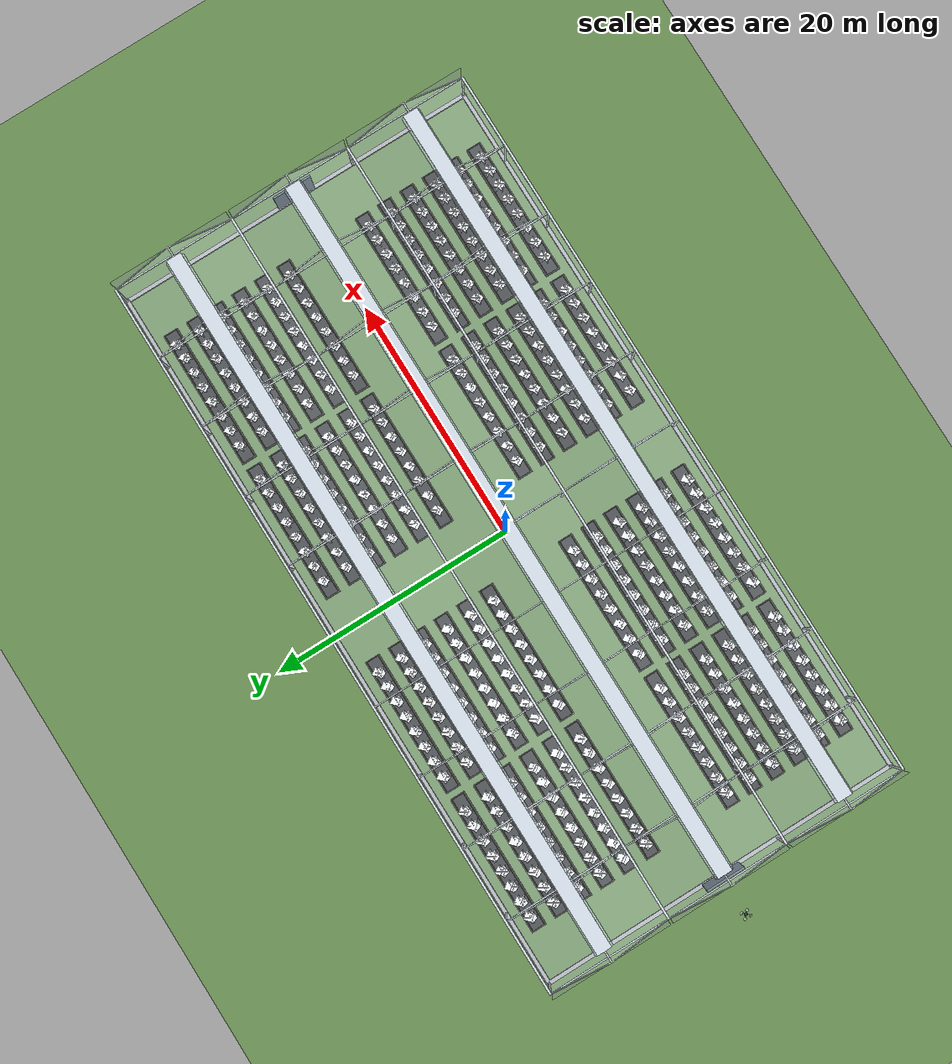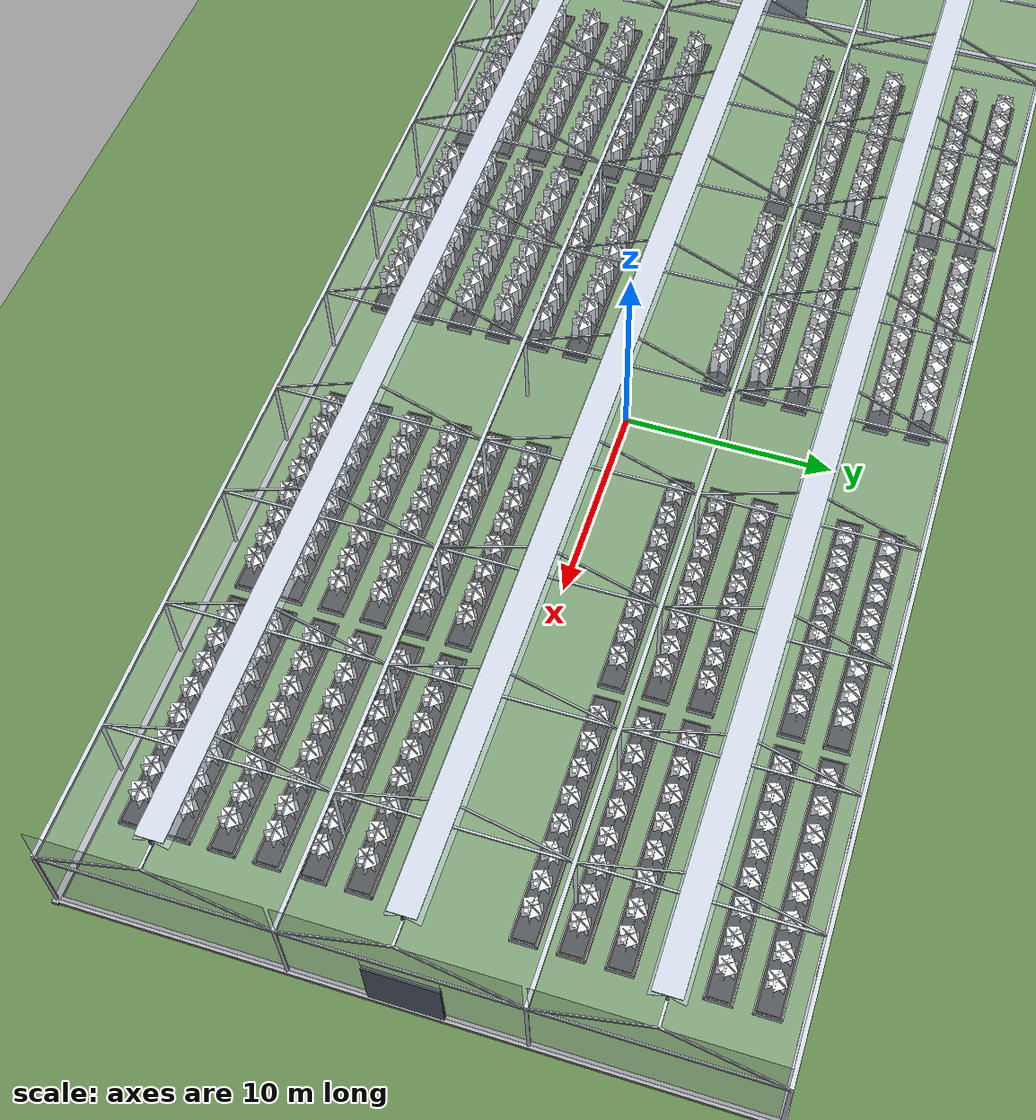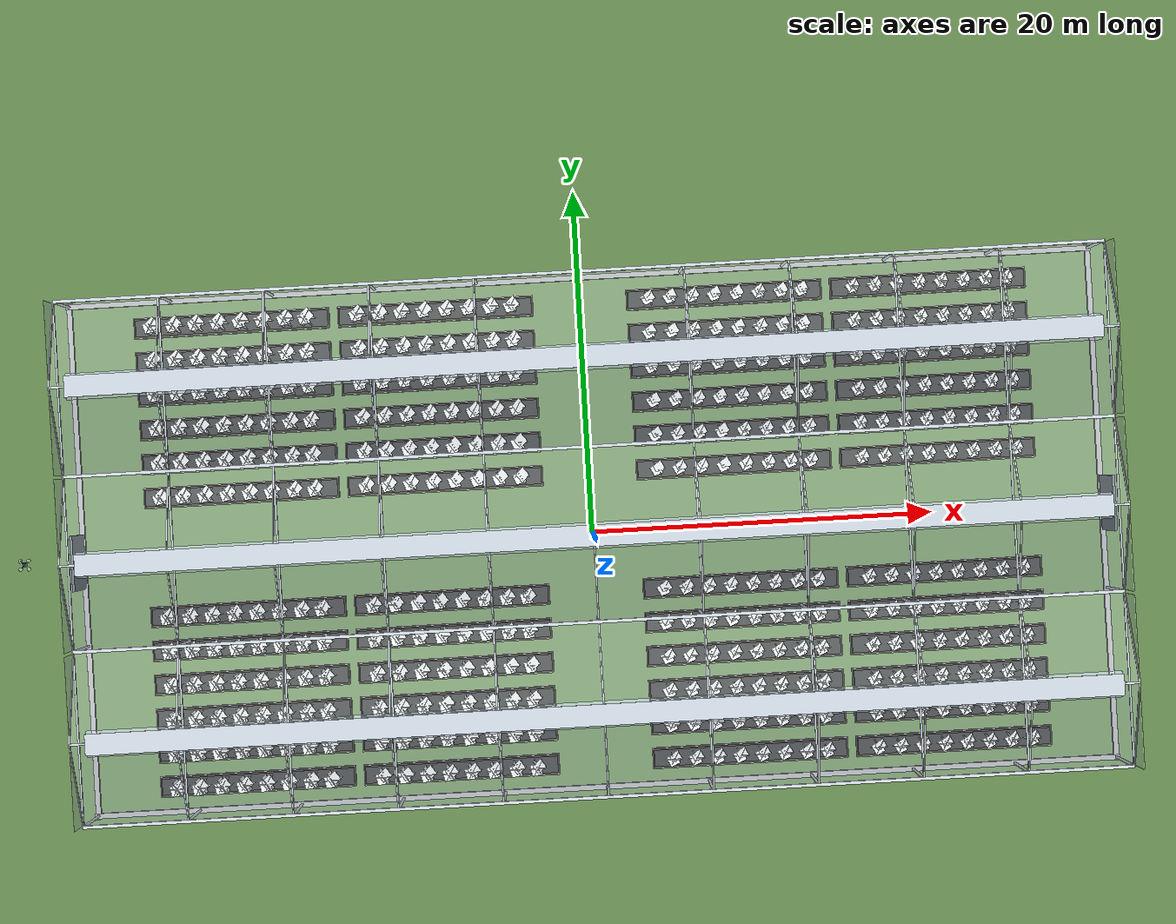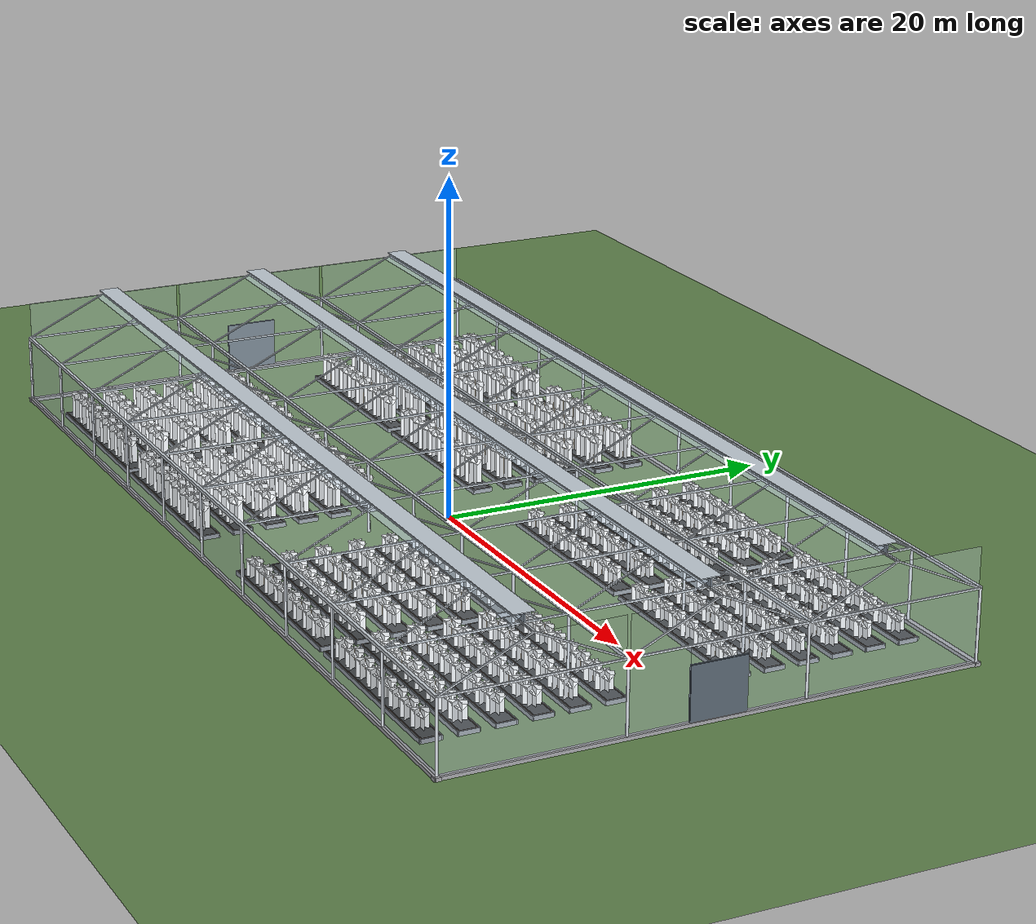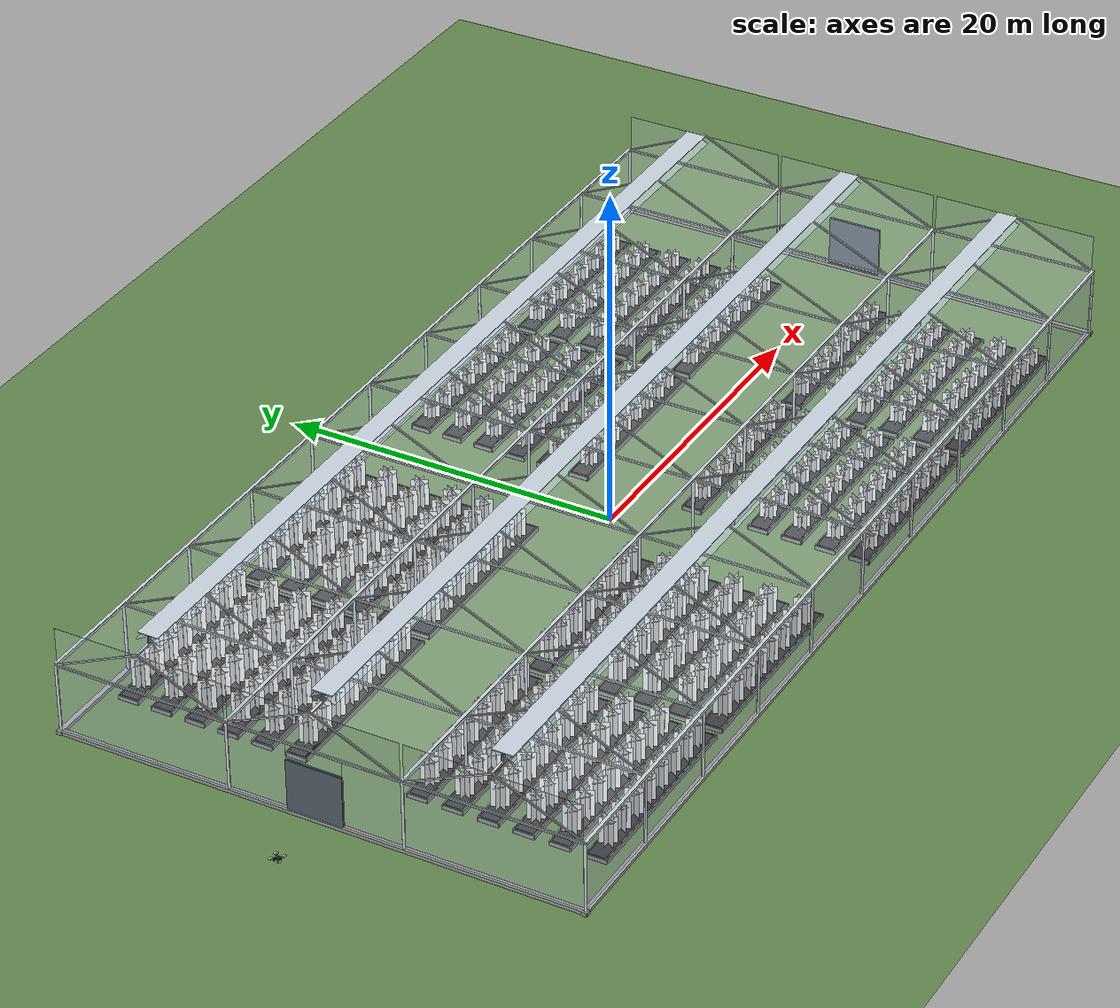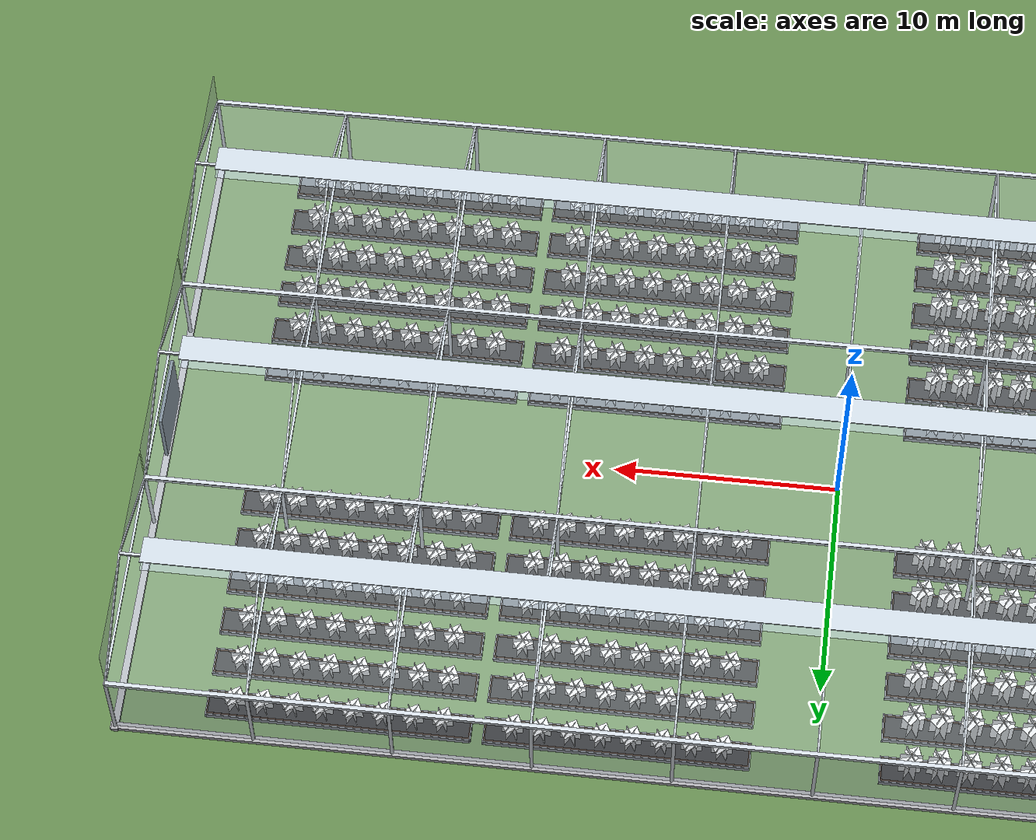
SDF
<?xml version="1.0" ?>
<sdf version="1.9">
  <world name="polyhouse_world">
    <!-- Physics Configuration -->
    <physics name="1ms" type="ignored">
      <max_step_size>0.001</max_step_size>
      <real_time_factor>1.0</real_time_factor>
    </physics>

    <!-- Plugins for Gazebo Harmonic -->
    <plugin filename="gz-sim-physics-system" name="gz::sim::systems::Physics" />
    <plugin filename="gz-sim-user-commands-system" name="gz::sim::systems::UserCommands" />
    <plugin filename="gz-sim-scene-broadcaster-system" name="gz::sim::systems::SceneBroadcaster" />
    <plugin filename="gz-sim-sensors-system" name="gz::sim::systems::Sensors">
      <render_engine>ogre2</render_engine>
    </plugin>

    <!-- Scene & Lighting -->
    <scene>
      <ambient>0.7 0.73 0.75 1.0</ambient>
      <background>0.7 0.85 0.95 1.0</background>
      <shadows>true</shadows>
      <grid>false</grid>
    </scene>

    <!-- Gazebo Sim GUI 3D Viewport Configuration -->
    <gui fullscreen="0">
      <!-- Full 3D Interactive Scene Plugin -->
      <plugin filename="GzScene3D" name="3D View">
        <gz-gui>
          <title>3D View</title>
          <property type="bool" key="showTitleBar">false</property>
          <property type="string" key="state">docked</property>
        </gz-gui>
        <engine>ogre2</engine>
        <scene>scene</scene>
        <ambient_light>0.7 0.73 0.75</ambient_light>
        <background_color>0.7 0.85 0.95</background_color>
        <camera_pose>0 -45 28 0 0.55 1.5708</camera_pose>
      </plugin>

      <!-- Interactive View Control (Orbit, Pan, Zoom) -->
      <plugin filename="InteractiveViewControl" name="Interactive view control">
        <gz-gui>
          <property type="bool" key="showTitleBar">false</property>
          <property type="string" key="state">docked</property>
        </gz-gui>
      </plugin>

      <!-- World Control (Play, Pause, Step) -->
      <plugin filename="WorldControl" name="World control">
        <gz-gui>
          <title>World control</title>
          <property type="bool" key="showTitleBar">false</property>
          <property type="bool" key="resizable">false</property>
          <property type="double" key="height">72</property>
          <property type="double" key="width">121</property>
          <property type="double" key="z">1</property>
          <property type="string" key="state">floating</property>
          <anchors target="3D View">
            <line own="left" target="left"/>
            <line own="bottom" target="bottom"/>
          </anchors>
        </gz-gui>
        <play_pause>true</play_pause>
        <step>true</step>
        <start_paused>false</start_paused>
      </plugin>

      <!-- World Stats (Sim Time, Real Time Factor) -->
      <plugin filename="WorldStats" name="World stats">
        <gz-gui>
          <title>World stats</title>
          <property type="bool" key="showTitleBar">false</property>
          <property type="bool" key="resizable">false</property>
          <property type="double" key="height">110</property>
          <property type="double" key="width">290</property>
          <property type="double" key="z">1</property>
          <property type="string" key="state">floating</property>
          <anchors target="3D View">
            <line own="right" target="right"/>
            <line own="bottom" target="bottom"/>
          </anchors>
        </gz-gui>
        <sim_time>true</sim_time>
        <real_time>true</real_time>
        <real_time_factor>true</real_time_factor>
        <iterations>true</iterations>
      </plugin>

      <!-- Entity Tree & Component Inspector -->
      <plugin filename="EntityTree" name="Entity tree">
        <gz-gui>
          <property type="string" key="state">docked</property>
        </gz-gui>
      </plugin>
    </gui>

    <!-- Sunlight -->
    <light type="directional" name="sun">
      <cast_shadows>true</cast_shadows>
      <pose>15 -20 35 0.5 0.3 -0.8</pose>
      <diffuse>0.92 0.92 0.88 1</diffuse>
      <specular>0.3 0.3 0.3 1</specular>
      <direction>-0.3 0.4 -0.85</direction>
    </light>

    <!-- Secondary Fill Light inside Polyhouse -->
    <light type="directional" name="diffuse_sky">
      <cast_shadows>false</cast_shadows>
      <pose>0 0 20 0 0 0</pose>
      <diffuse>0.4 0.42 0.45 1</diffuse>
      <direction>0 0 -1</direction>
    </light>

    <!-- Ground Plane & Surrounding Terrain -->
    <model name="ground_plane">
      <static>true</static>
      <link name="ground_link">
        <collision name="ground_collision">
          <geometry><plane><normal>0 0 1</normal><size>150 150</size></plane></geometry>
        </collision>
        <!-- Surrounding Farmland Surface -->
        <visual name="ground_visual">
          <geometry><plane><normal>0 0 1</normal><size>150 150</size></plane></geometry>
          <material>
            <ambient>0.32 0.45 0.25 1</ambient>
            <diffuse>0.38 0.52 0.3 1</diffuse>
            <roughness>0.9</roughness>
          </material>
        </visual>
        <!-- Polyhouse Internal Foundation Floor (60m x 30m) -->
        <visual name="polyhouse_floor">
          <pose>0 0 0.005 0 0 0</pose>
          <geometry><box><size>60.2 30.2 0.01</size></box></geometry>
          <material>
            <ambient>0.28 0.22 0.18 1</ambient>
            <diffuse>0.34 0.27 0.22 1</diffuse>
            <roughness>0.95</roughness>
          </material>
        </visual>
        <!-- Central Longitudinal Concrete Walkway (60m x 3m) -->
        <visual name="main_walkway_longitudinal">
          <pose>0 0 0.015 0 0 0</pose>
          <geometry><box><size>60.0 3.0 0.02</size></box></geometry>
          <material>
            <ambient>0.62 0.64 0.65 1</ambient>
            <diffuse>0.72 0.74 0.75 1</diffuse>
            <roughness>0.7</roughness>
          </material>
        </visual>
        <!-- Transverse Cross Walkway (3m x 30m) -->
        <visual name="main_walkway_transverse">
          <pose>0 0 0.016 0 0 0</pose>
          <geometry><box><size>3.0 30.0 0.02</size></box></geometry>
          <material>
            <ambient>0.62 0.64 0.65 1</ambient>
            <diffuse>0.72 0.74 0.75 1</diffuse>
            <roughness>0.7</roughness>
          </material>
        </visual>
      </link>
    </model>

    <!-- POLYHOUSE ARCHITECTURAL MODELS             -->
    <!-- 1. Structural Steel Frame -->
    <include>
      <uri>model://polyhouse_structure</uri>
      <name>polyhouse_main</name>
      <pose>0 0 0 0 0 0</pose>
    </include>

    <!-- 2. Translucent Greenhouse Polyethylene Cladding -->
    <include>
      <uri>model://polyhouse_covering</uri>
      <name>polyhouse_covering_main</name>
      <pose>0 0 0 0 0 0</pose>
    </include>

    <!-- 3. Rooftop Ventilation System -->
    <include>
      <uri>model://rooftop_ventilation</uri>
      <name>polyhouse_ventilation_system</name>
      <pose>0 0 0 0 0 0</pose>
    </include>

    <!-- ZONE: TOMATO_ZONE_01 (TOMATO) -->
    <include>
      <uri>model://crop_bed</uri>
      <name>tomato_bed_001</name>
      <pose>-20.5 3.5 0 0 0 0</pose>
    </include>
    <include>
      <uri>model://tomato_plant</uri>
      <name>tomato_bed_001_p01</name>
      <pose>-25.00 3.5 0.25 0 0 0</pose>
    </include>
    <include>
      <uri>model://tomato_plant</uri>
      <name>tomato_bed_001_p02</name>
      <pose>-23.70 3.5 0.25 0 0 0</pose>
    </include>
    <include>
      <uri>model://tomato_plant</uri>
      <name>tomato_bed_001_p03</name>
      <pose>-22.40 3.5 0.25 0 0 0</pose>
    </include>
    <include>
      <uri>model://tomato_plant</uri>
      <name>tomato_bed_001_p04</name>
      <pose>-21.10 3.5 0.25 0 0 0</pose>
    </include>
    <include>
      <uri>model://tomato_plant</uri>
      <name>tomato_bed_001_p05</name>
      <pose>-19.80 3.5 0.25 0 0 0</pose>
    </include>
    <include>
      <uri>model://tomato_plant</uri>
      <name>tomato_bed_001_p06</name>
      <pose>-18.50 3.5 0.25 0 0 0</pose>
    </include>
    <include>
      <uri>model://tomato_plant</uri>
      <name>tomato_bed_001_p07</name>
      <pose>-17.20 3.5 0.25 0 0 0</pose>
    </include>
    <include>
      <uri>model://tomato_plant</uri>
      <name>tomato_bed_001_p08</name>
      <pose>-16.00 3.5 0.25 0 0 0</pose>
    </include>

    <include>
      <uri>model://crop_bed</uri>
      <name>tomato_bed_002</name>
      <pose>-8.5 3.5 0 0 0 0</pose>
    </include>
    <include>
      <uri>model://tomato_plant</uri>
      <name>tomato_bed_002_p01</name>
      <pose>-13.00 3.5 0.25 0 0 0</pose>
    </include>
    <include>
      <uri>model://tomato_plant</uri>
      <name>tomato_bed_002_p02</name>
      <pose>-11.70 3.5 0.25 0 0 0</pose>
    </include>
    <include>
      <uri>model://tomato_plant</uri>
      <name>tomato_bed_002_p03</name>
      <pose>-10.40 3.5 0.25 0 0 0</pose>
    </include>
    <include>
      <uri>model://tomato_plant</uri>
      <name>tomato_bed_002_p04</name>
      <pose>-9.10 3.5 0.25 0 0 0</pose>
    </include>
    <include>
      <uri>model://tomato_plant</uri>
      <name>tomato_bed_002_p05</name>
      <pose>-7.80 3.5 0.25 0 0 0</pose>
    </include>
    <include>
      <uri>model://tomato_plant</uri>
      <name>tomato_bed_002_p06</name>
      <pose>-6.50 3.5 0.25 0 0 0</pose>
    </include>
    <include>
      <uri>model://tomato_plant</uri>
      <name>tomato_bed_002_p07</name>
      <pose>-5.20 3.5 0.25 0 0 0</pose>
    </include>
    <include>
      <uri>model://tomato_plant</uri>
      <name>tomato_bed_002_p08</name>
      <pose>-4.00 3.5 0.25 0 0 0</pose>
    </include>

    <include>
      <uri>model://crop_bed</uri>
      <name>tomato_bed_003</name>
      <pose>-20.5 5.5 0 0 0 0</pose>
    </include>
    <include>
      <uri>model://tomato_plant</uri>
      <name>tomato_bed_003_p01</name>
      <pose>-25.00 5.5 0.25 0 0 0</pose>
    </include>
    <include>
      <uri>model://tomato_plant</uri>
      <name>tomato_bed_003_p02</name>
      <pose>-23.70 5.5 0.25 0 0 0</pose>
    </include>
    <include>
      <uri>model://tomato_plant</uri>
      <name>tomato_bed_003_p03</name>
      <pose>-22.40 5.5 0.25 0 0 0</pose>
    </include>
    <include>
      <uri>model://tomato_plant</uri>
      <name>tomato_bed_003_p04</name>
      <pose>-21.10 5.5 0.25 0 0 0</pose>
    </include>
    <include>
      <uri>model://tomato_plant</uri>
      <name>tomato_bed_003_p05</name>
      <pose>-19.80 5.5 0.25 0 0 0</pose>
    </include>
    <include>
      <uri>model://tomato_plant</uri>
      <name>tomato_bed_003_p06</name>
      <pose>-18.50 5.5 0.25 0 0 0</pose>
    </include>
    <include>
      <uri>model://tomato_plant</uri>
      <name>tomato_bed_003_p07</name>
      <pose>-17.20 5.5 0.25 0 0 0</pose>
    </include>
    <include>
      <uri>model://tomato_plant</uri>
      <name>tomato_bed_003_p08</name>
      <pose>-16.00 5.5 0.25 0 0 0</pose>
    </include>

    <include>
      <uri>model://crop_bed</uri>
      <name>tomato_bed_004</name>
      <pose>-8.5 5.5 0 0 0 0</pose>
    </include>
    <include>
      <uri>model://tomato_plant</uri>
      <name>tomato_bed_004_p01</name>
      <pose>-13.00 5.5 0.25 0 0 0</pose>
    </include>
    <include>
      <uri>model://tomato_plant</uri>
      <name>tomato_bed_004_p02</name>
      <pose>-11.70 5.5 0.25 0 0 0</pose>
    </include>
    <include>
      <uri>model://tomato_plant</uri>
      <name>tomato_bed_004_p03</name>
      <pose>-10.40 5.5 0.25 0 0 0</pose>
    </include>
    <include>
      <uri>model://tomato_plant</uri>
      <name>tomato_bed_004_p04</name>
      <pose>-9.10 5.5 0.25 0 0 0</pose>
    </include>
    <include>
      <uri>model://tomato_plant</uri>
      <name>tomato_bed_004_p05</name>
      <pose>-7.80 5.5 0.25 0 0 0</pose>
    </include>
    <include>
      <uri>model://tomato_plant</uri>
      <name>tomato_bed_004_p06</name>
      <pose>-6.50 5.5 0.25 0 0 0</pose>
    </include>
    <include>
      <uri>model://tomato_plant</uri>
      <name>tomato_bed_004_p07</name>
      <pose>-5.20 5.5 0.25 0 0 0</pose>
    </include>
    <include>
      <uri>model://tomato_plant</uri>
      <name>tomato_bed_004_p08</name>
      <pose>-4.00 5.5 0.25 0 0 0</pose>
    </include>

    <include>
      <uri>model://crop_bed</uri>
      <name>tomato_bed_005</name>
      <pose>-20.5 7.5 0 0 0 0</pose>
    </include>
    <include>
      <uri>model://tomato_plant</uri>
      <name>tomato_bed_005_p01</name>
      <pose>-25.00 7.5 0.25 0 0 0</pose>
    </include>
    <include>
      <uri>model://tomato_plant</uri>
      <name>tomato_bed_005_p02</name>
      <pose>-23.70 7.5 0.25 0 0 0</pose>
    </include>
    <include>
      <uri>model://tomato_plant</uri>
      <name>tomato_bed_005_p03</name>
      <pose>-22.40 7.5 0.25 0 0 0</pose>
    </include>
    <include>
      <uri>model://tomato_plant</uri>
      <name>tomato_bed_005_p04</name>
      <pose>-21.10 7.5 0.25 0 0 0</pose>
    </include>
    <include>
      <uri>model://tomato_plant</uri>
      <name>tomato_bed_005_p05</name>
      <pose>-19.80 7.5 0.25 0 0 0</pose>
    </include>
    <include>
      <uri>model://tomato_plant</uri>
      <name>tomato_bed_005_p06</name>
      <pose>-18.50 7.5 0.25 0 0 0</pose>
    </include>
    <include>
      <uri>model://tomato_plant</uri>
      <name>tomato_bed_005_p07</name>
      <pose>-17.20 7.5 0.25 0 0 0</pose>
    </include>
    <include>
      <uri>model://tomato_plant</uri>
      <name>tomato_bed_005_p08</name>
      <pose>-16.00 7.5 0.25 0 0 0</pose>
    </include>

    <include>
      <uri>model://crop_bed</uri>
      <name>tomato_bed_006</name>
      <pose>-8.5 7.5 0 0 0 0</pose>
    </include>
    <include>
      <uri>model://tomato_plant</uri>
      <name>tomato_bed_006_p01</name>
      <pose>-13.00 7.5 0.25 0 0 0</pose>
    </include>
    <include>
      <uri>model://tomato_plant</uri>
      <name>tomato_bed_006_p02</name>
      <pose>-11.70 7.5 0.25 0 0 0</pose>
    </include>
    <include>
      <uri>model://tomato_plant</uri>
      <name>tomato_bed_006_p03</name>
      <pose>-10.40 7.5 0.25 0 0 0</pose>
    </include>
    <include>
      <uri>model://tomato_plant</uri>
      <name>tomato_bed_006_p04</name>
      <pose>-9.10 7.5 0.25 0 0 0</pose>
    </include>
    <include>
      <uri>model://tomato_plant</uri>
      <name>tomato_bed_006_p05</name>
      <pose>-7.80 7.5 0.25 0 0 0</pose>
    </include>
    <include>
      <uri>model://tomato_plant</uri>
      <name>tomato_bed_006_p06</name>
      <pose>-6.50 7.5 0.25 0 0 0</pose>
    </include>
    <include>
      <uri>model://tomato_plant</uri>
      <name>tomato_bed_006_p07</name>
      <pose>-5.20 7.5 0.25 0 0 0</pose>
    </include>
    <include>
      <uri>model://tomato_plant</uri>
      <name>tomato_bed_006_p08</name>
      <pose>-4.00 7.5 0.25 0 0 0</pose>
    </include>

    <include>
      <uri>model://crop_bed</uri>
      <name>tomato_bed_007</name>
      <pose>-20.5 9.5 0 0 0 0</pose>
    </include>
    <include>
      <uri>model://tomato_plant</uri>
      <name>tomato_bed_007_p01</name>
      <pose>-25.00 9.5 0.25 0 0 0</pose>
    </include>
    <include>
      <uri>model://tomato_plant</uri>
      <name>tomato_bed_007_p02</name>
      <pose>-23.70 9.5 0.25 0 0 0</pose>
    </include>
    <include>
      <uri>model://tomato_plant</uri>
      <name>tomato_bed_007_p03</name>
      <pose>-22.40 9.5 0.25 0 0 0</pose>
    </include>
    <include>
      <uri>model://tomato_plant</uri>
      <name>tomato_bed_007_p04</name>
      <pose>-21.10 9.5 0.25 0 0 0</pose>
    </include>
    <include>
      <uri>model://tomato_plant</uri>
      <name>tomato_bed_007_p05</name>
      <pose>-19.80 9.5 0.25 0 0 0</pose>
    </include>
    <include>
      <uri>model://tomato_plant</uri>
      <name>tomato_bed_007_p06</name>
      <pose>-18.50 9.5 0.25 0 0 0</pose>
    </include>
    <include>
      <uri>model://tomato_plant</uri>
      <name>tomato_bed_007_p07</name>
      <pose>-17.20 9.5 0.25 0 0 0</pose>
    </include>
    <include>
      <uri>model://tomato_plant</uri>
      <name>tomato_bed_007_p08</name>
      <pose>-16.00 9.5 0.25 0 0 0</pose>
    </include>

    <include>
      <uri>model://crop_bed</uri>
      <name>tomato_bed_008</name>
      <pose>-8.5 9.5 0 0 0 0</pose>
    </include>
    <include>
      <uri>model://tomato_plant</uri>
      <name>tomato_bed_008_p01</name>
      <pose>-13.00 9.5 0.25 0 0 0</pose>
    </include>
    <include>
      <uri>model://tomato_plant</uri>
      <name>tomato_bed_008_p02</name>
      <pose>-11.70 9.5 0.25 0 0 0</pose>
    </include>
    <include>
      <uri>model://tomato_plant</uri>
      <name>tomato_bed_008_p03</name>
      <pose>-10.40 9.5 0.25 0 0 0</pose>
    </include>
    <include>
      <uri>model://tomato_plant</uri>
      <name>tomato_bed_008_p04</name>
      <pose>-9.10 9.5 0.25 0 0 0</pose>
    </include>
    <include>
      <uri>model://tomato_plant</uri>
      <name>tomato_bed_008_p05</name>
      <pose>-7.80 9.5 0.25 0 0 0</pose>
    </include>
    <include>
      <uri>model://tomato_plant</uri>
      <name>tomato_bed_008_p06</name>
      <pose>-6.50 9.5 0.25 0 0 0</pose>
    </include>
    <include>
      <uri>model://tomato_plant</uri>
      <name>tomato_bed_008_p07</name>
      <pose>-5.20 9.5 0.25 0 0 0</pose>
    </include>
    <include>
      <uri>model://tomato_plant</uri>
      <name>tomato_bed_008_p08</name>
      <pose>-4.00 9.5 0.25 0 0 0</pose>
    </include>

    <include>
      <uri>model://crop_bed</uri>
      <name>tomato_bed_009</name>
      <pose>-20.5 11.5 0 0 0 0</pose>
    </include>
    <include>
      <uri>model://tomato_plant</uri>
      <name>tomato_bed_009_p01</name>
      <pose>-25.00 11.5 0.25 0 0 0</pose>
    </include>
    <include>
      <uri>model://tomato_plant</uri>
      <name>tomato_bed_009_p02</name>
      <pose>-23.70 11.5 0.25 0 0 0</pose>
    </include>
    <include>
      <uri>model://tomato_plant</uri>
      <name>tomato_bed_009_p03</name>
      <pose>-22.40 11.5 0.25 0 0 0</pose>
    </include>
    <include>
      <uri>model://tomato_plant</uri>
      <name>tomato_bed_009_p04</name>
      <pose>-21.10 11.5 0.25 0 0 0</pose>
    </include>
    <include>
      <uri>model://tomato_plant</uri>
      <name>tomato_bed_009_p05</name>
      <pose>-19.80 11.5 0.25 0 0 0</pose>
    </include>
    <include>
      <uri>model://tomato_plant</uri>
      <name>tomato_bed_009_p06</name>
      <pose>-18.50 11.5 0.25 0 0 0</pose>
    </include>
    <include>
      <uri>model://tomato_plant</uri>
      <name>tomato_bed_009_p07</name>
      <pose>-17.20 11.5 0.25 0 0 0</pose>
    </include>
    <include>
      <uri>model://tomato_plant</uri>
      <name>tomato_bed_009_p08</name>
      <pose>-16.00 11.5 0.25 0 0 0</pose>
    </include>

    <include>
      <uri>model://crop_bed</uri>
      <name>tomato_bed_010</name>
      <pose>-8.5 11.5 0 0 0 0</pose>
    </include>
    <include>
      <uri>model://tomato_plant</uri>
      <name>tomato_bed_010_p01</name>
      <pose>-13.00 11.5 0.25 0 0 0</pose>
    </include>
    <include>
      <uri>model://tomato_plant</uri>
      <name>tomato_bed_010_p02</name>
      <pose>-11.70 11.5 0.25 0 0 0</pose>
    </include>
    <include>
      <uri>model://tomato_plant</uri>
      <name>tomato_bed_010_p03</name>
      <pose>-10.40 11.5 0.25 0 0 0</pose>
    </include>
    <include>
      <uri>model://tomato_plant</uri>
      <name>tomato_bed_010_p04</name>
      <pose>-9.10 11.5 0.25 0 0 0</pose>
    </include>
    <include>
      <uri>model://tomato_plant</uri>
      <name>tomato_bed_010_p05</name>
      <pose>-7.80 11.5 0.25 0 0 0</pose>
    </include>
    <include>
      <uri>model://tomato_plant</uri>
      <name>tomato_bed_010_p06</name>
      <pose>-6.50 11.5 0.25 0 0 0</pose>
    </include>
    <include>
      <uri>model://tomato_plant</uri>
      <name>tomato_bed_010_p07</name>
      <pose>-5.20 11.5 0.25 0 0 0</pose>
    </include>
    <include>
      <uri>model://tomato_plant</uri>
      <name>tomato_bed_010_p08</name>
      <pose>-4.00 11.5 0.25 0 0 0</pose>
    </include>

    <include>
      <uri>model://crop_bed</uri>
      <name>tomato_bed_011</name>
      <pose>-20.5 13.5 0 0 0 0</pose>
    </include>
    <include>
      <uri>model://tomato_plant</uri>
      <name>tomato_bed_011_p01</name>
      <pose>-25.00 13.5 0.25 0 0 0</pose>
    </include>
    <include>
      <uri>model://tomato_plant</uri>
      <name>tomato_bed_011_p02</name>
      <pose>-23.70 13.5 0.25 0 0 0</pose>
    </include>
    <include>
      <uri>model://tomato_plant</uri>
      <name>tomato_bed_011_p03</name>
      <pose>-22.40 13.5 0.25 0 0 0</pose>
    </include>
    <include>
      <uri>model://tomato_plant</uri>
      <name>tomato_bed_011_p04</name>
      <pose>-21.10 13.5 0.25 0 0 0</pose>
    </include>
    <include>
      <uri>model://tomato_plant</uri>
      <name>tomato_bed_011_p05</name>
      <pose>-19.80 13.5 0.25 0 0 0</pose>
    </include>
    <include>
      <uri>model://tomato_plant</uri>
      <name>tomato_bed_011_p06</name>
      <pose>-18.50 13.5 0.25 0 0 0</pose>
    </include>
    <include>
      <uri>model://tomato_plant</uri>
      <name>tomato_bed_011_p07</name>
      <pose>-17.20 13.5 0.25 0 0 0</pose>
    </include>
    <include>
      <uri>model://tomato_plant</uri>
      <name>tomato_bed_011_p08</name>
      <pose>-16.00 13.5 0.25 0 0 0</pose>
    </include>

    <include>
      <uri>model://crop_bed</uri>
      <name>tomato_bed_012</name>
      <pose>-8.5 13.5 0 0 0 0</pose>
    </include>
    <include>
      <uri>model://tomato_plant</uri>
      <name>tomato_bed_012_p01</name>
      <pose>-13.00 13.5 0.25 0 0 0</pose>
    </include>
    <include>
      <uri>model://tomato_plant</uri>
      <name>tomato_bed_012_p02</name>
      <pose>-11.70 13.5 0.25 0 0 0</pose>
    </include>
    <include>
      <uri>model://tomato_plant</uri>
      <name>tomato_bed_012_p03</name>
      <pose>-10.40 13.5 0.25 0 0 0</pose>
    </include>
    <include>
      <uri>model://tomato_plant</uri>
      <name>tomato_bed_012_p04</name>
      <pose>-9.10 13.5 0.25 0 0 0</pose>
    </include>
    <include>
      <uri>model://tomato_plant</uri>
      <name>tomato_bed_012_p05</name>
      <pose>-7.80 13.5 0.25 0 0 0</pose>
    </include>
    <include>
      <uri>model://tomato_plant</uri>
      <name>tomato_bed_012_p06</name>
      <pose>-6.50 13.5 0.25 0 0 0</pose>
    </include>
    <include>
      <uri>model://tomato_plant</uri>
      <name>tomato_bed_012_p07</name>
      <pose>-5.20 13.5 0.25 0 0 0</pose>
    </include>
    <include>
      <uri>model://tomato_plant</uri>
      <name>tomato_bed_012_p08</name>
      <pose>-4.00 13.5 0.25 0 0 0</pose>
    </include>

    <!-- ZONE: CAPSICUM_ZONE_01 (CAPSICUM) -->
    <include>
      <uri>model://crop_bed</uri>
      <name>capsicum_bed_001</name>
      <pose>8.5 3.5 0 0 0 0</pose>
    </include>
    <include>
      <uri>model://capsicum_plant</uri>
      <name>capsicum_bed_001_p01</name>
      <pose>4.00 3.5 0.25 0 0 0</pose>
    </include>
    <include>
      <uri>model://capsicum_plant</uri>
      <name>capsicum_bed_001_p02</name>
      <pose>5.30 3.5 0.25 0 0 0</pose>
    </include>
    <include>
      <uri>model://capsicum_plant</uri>
      <name>capsicum_bed_001_p03</name>
      <pose>6.60 3.5 0.25 0 0 0</pose>
    </include>
    <include>
      <uri>model://capsicum_plant</uri>
      <name>capsicum_bed_001_p04</name>
      <pose>7.90 3.5 0.25 0 0 0</pose>
    </include>
    <include>
      <uri>model://capsicum_plant</uri>
      <name>capsicum_bed_001_p05</name>
      <pose>9.20 3.5 0.25 0 0 0</pose>
    </include>
    <include>
      <uri>model://capsicum_plant</uri>
      <name>capsicum_bed_001_p06</name>
      <pose>10.50 3.5 0.25 0 0 0</pose>
    </include>
    <include>
      <uri>model://capsicum_plant</uri>
      <name>capsicum_bed_001_p07</name>
      <pose>11.80 3.5 0.25 0 0 0</pose>
    </include>
    <include>
      <uri>model://capsicum_plant</uri>
      <name>capsicum_bed_001_p08</name>
      <pose>13.00 3.5 0.25 0 0 0</pose>
    </include>

    <include>
      <uri>model://crop_bed</uri>
      <name>capsicum_bed_002</name>
      <pose>20.5 3.5 0 0 0 0</pose>
    </include>
    <include>
      <uri>model://capsicum_plant</uri>
      <name>capsicum_bed_002_p01</name>
      <pose>16.00 3.5 0.25 0 0 0</pose>
    </include>
    <include>
      <uri>model://capsicum_plant</uri>
      <name>capsicum_bed_002_p02</name>
      <pose>17.30 3.5 0.25 0 0 0</pose>
    </include>
    <include>
      <uri>model://capsicum_plant</uri>
      <name>capsicum_bed_002_p03</name>
      <pose>18.60 3.5 0.25 0 0 0</pose>
    </include>
    <include>
      <uri>model://capsicum_plant</uri>
      <name>capsicum_bed_002_p04</name>
      <pose>19.90 3.5 0.25 0 0 0</pose>
    </include>
    <include>
      <uri>model://capsicum_plant</uri>
      <name>capsicum_bed_002_p05</name>
      <pose>21.20 3.5 0.25 0 0 0</pose>
    </include>
    <include>
      <uri>model://capsicum_plant</uri>
      <name>capsicum_bed_002_p06</name>
      <pose>22.50 3.5 0.25 0 0 0</pose>
    </include>
    <include>
      <uri>model://capsicum_plant</uri>
      <name>capsicum_bed_002_p07</name>
      <pose>23.80 3.5 0.25 0 0 0</pose>
    </include>
    <include>
      <uri>model://capsicum_plant</uri>
      <name>capsicum_bed_002_p08</name>
      <pose>25.00 3.5 0.25 0 0 0</pose>
    </include>

    <include>
      <uri>model://crop_bed</uri>
      <name>capsicum_bed_003</name>
      <pose>8.5 5.5 0 0 0 0</pose>
    </include>
    <include>
      <uri>model://capsicum_plant</uri>
      <name>capsicum_bed_003_p01</name>
      <pose>4.00 5.5 0.25 0 0 0</pose>
    </include>
    <include>
      <uri>model://capsicum_plant</uri>
      <name>capsicum_bed_003_p02</name>
      <pose>5.30 5.5 0.25 0 0 0</pose>
    </include>
    <include>
      <uri>model://capsicum_plant</uri>
      <name>capsicum_bed_003_p03</name>
      <pose>6.60 5.5 0.25 0 0 0</pose>
    </include>
    <include>
      <uri>model://capsicum_plant</uri>
      <name>capsicum_bed_003_p04</name>
      <pose>7.90 5.5 0.25 0 0 0</pose>
    </include>
    <include>
      <uri>model://capsicum_plant</uri>
      <name>capsicum_bed_003_p05</name>
      <pose>9.20 5.5 0.25 0 0 0</pose>
    </include>
    <include>
      <uri>model://capsicum_plant</uri>
      <name>capsicum_bed_003_p06</name>
      <pose>10.50 5.5 0.25 0 0 0</pose>
    </include>
    <include>
      <uri>model://capsicum_plant</uri>
      <name>capsicum_bed_003_p07</name>
      <pose>11.80 5.5 0.25 0 0 0</pose>
    </include>
    <include>
      <uri>model://capsicum_plant</uri>
      <name>capsicum_bed_003_p08</name>
      <pose>13.00 5.5 0.25 0 0 0</pose>
    </include>

    <include>
      <uri>model://crop_bed</uri>
      <name>capsicum_bed_004</name>
      <pose>20.5 5.5 0 0 0 0</pose>
    </include>
    <include>
      <uri>model://capsicum_plant</uri>
      <name>capsicum_bed_004_p01</name>
      <pose>16.00 5.5 0.25 0 0 0</pose>
    </include>
    <include>
      <uri>model://capsicum_plant</uri>
      <name>capsicum_bed_004_p02</name>
      <pose>17.30 5.5 0.25 0 0 0</pose>
    </include>
    <include>
      <uri>model://capsicum_plant</uri>
      <name>capsicum_bed_004_p03</name>
      <pose>18.60 5.5 0.25 0 0 0</pose>
    </include>
    <include>
      <uri>model://capsicum_plant</uri>
      <name>capsicum_bed_004_p04</name>
      <pose>19.90 5.5 0.25 0 0 0</pose>
    </include>
    <include>
      <uri>model://capsicum_plant</uri>
      <name>capsicum_bed_004_p05</name>
      <pose>21.20 5.5 0.25 0 0 0</pose>
    </include>
    <include>
      <uri>model://capsicum_plant</uri>
      <name>capsicum_bed_004_p06</name>
      <pose>22.50 5.5 0.25 0 0 0</pose>
    </include>
    <include>
      <uri>model://capsicum_plant</uri>
      <name>capsicum_bed_004_p07</name>
      <pose>23.80 5.5 0.25 0 0 0</pose>
    </include>
    <include>
      <uri>model://capsicum_plant</uri>
      <name>capsicum_bed_004_p08</name>
      <pose>25.00 5.5 0.25 0 0 0</pose>
    </include>

    <include>
      <uri>model://crop_bed</uri>
      <name>capsicum_bed_005</name>
      <pose>8.5 7.5 0 0 0 0</pose>
    </include>
    <include>
      <uri>model://capsicum_plant</uri>
      <name>capsicum_bed_005_p01</name>
      <pose>4.00 7.5 0.25 0 0 0</pose>
    </include>
    <include>
      <uri>model://capsicum_plant</uri>
      <name>capsicum_bed_005_p02</name>
      <pose>5.30 7.5 0.25 0 0 0</pose>
    </include>
    <include>
      <uri>model://capsicum_plant</uri>
      <name>capsicum_bed_005_p03</name>
      <pose>6.60 7.5 0.25 0 0 0</pose>
    </include>
    <include>
      <uri>model://capsicum_plant</uri>
      <name>capsicum_bed_005_p04</name>
      <pose>7.90 7.5 0.25 0 0 0</pose>
    </include>
    <include>
      <uri>model://capsicum_plant</uri>
      <name>capsicum_bed_005_p05</name>
      <pose>9.20 7.5 0.25 0 0 0</pose>
    </include>
    <include>
      <uri>model://capsicum_plant</uri>
      <name>capsicum_bed_005_p06</name>
      <pose>10.50 7.5 0.25 0 0 0</pose>
    </include>
    <include>
      <uri>model://capsicum_plant</uri>
      <name>capsicum_bed_005_p07</name>
      <pose>11.80 7.5 0.25 0 0 0</pose>
    </include>
    <include>
      <uri>model://capsicum_plant</uri>
      <name>capsicum_bed_005_p08</name>
      <pose>13.00 7.5 0.25 0 0 0</pose>
    </include>

    <include>
      <uri>model://crop_bed</uri>
      <name>capsicum_bed_006</name>
      <pose>20.5 7.5 0 0 0 0</pose>
    </include>
    <include>
      <uri>model://capsicum_plant</uri>
      <name>capsicum_bed_006_p01</name>
      <pose>16.00 7.5 0.25 0 0 0</pose>
    </include>
    <include>
      <uri>model://capsicum_plant</uri>
      <name>capsicum_bed_006_p02</name>
      <pose>17.30 7.5 0.25 0 0 0</pose>
    </include>
    <include>
      <uri>model://capsicum_plant</uri>
      <name>capsicum_bed_006_p03</name>
      <pose>18.60 7.5 0.25 0 0 0</pose>
    </include>
    <include>
      <uri>model://capsicum_plant</uri>
      <name>capsicum_bed_006_p04</name>
      <pose>19.90 7.5 0.25 0 0 0</pose>
    </include>
    <include>
      <uri>model://capsicum_plant</uri>
      <name>capsicum_bed_006_p05</name>
      <pose>21.20 7.5 0.25 0 0 0</pose>
    </include>
    <include>
      <uri>model://capsicum_plant</uri>
      <name>capsicum_bed_006_p06</name>
      <pose>22.50 7.5 0.25 0 0 0</pose>
    </include>
    <include>
      <uri>model://capsicum_plant</uri>
      <name>capsicum_bed_006_p07</name>
      <pose>23.80 7.5 0.25 0 0 0</pose>
    </include>
    <include>
      <uri>model://capsicum_plant</uri>
      <name>capsicum_bed_006_p08</name>
      <pose>25.00 7.5 0.25 0 0 0</pose>
    </include>

    <include>
      <uri>model://crop_bed</uri>
      <name>capsicum_bed_007</name>
      <pose>8.5 9.5 0 0 0 0</pose>
    </include>
    <include>
      <uri>model://capsicum_plant</uri>
      <name>capsicum_bed_007_p01</name>
      <pose>4.00 9.5 0.25 0 0 0</pose>
    </include>
    <include>
      <uri>model://capsicum_plant</uri>
      <name>capsicum_bed_007_p02</name>
      <pose>5.30 9.5 0.25 0 0 0</pose>
    </include>
    <include>
      <uri>model://capsicum_plant</uri>
      <name>capsicum_bed_007_p03</name>
      <pose>6.60 9.5 0.25 0 0 0</pose>
    </include>
    <include>
      <uri>model://capsicum_plant</uri>
      <name>capsicum_bed_007_p04</name>
      <pose>7.90 9.5 0.25 0 0 0</pose>
    </include>
    <include>
      <uri>model://capsicum_plant</uri>
      <name>capsicum_bed_007_p05</name>
      <pose>9.20 9.5 0.25 0 0 0</pose>
    </include>
    <include>
      <uri>model://capsicum_plant</uri>
      <name>capsicum_bed_007_p06</name>
      <pose>10.50 9.5 0.25 0 0 0</pose>
    </include>
    <include>
      <uri>model://capsicum_plant</uri>
      <name>capsicum_bed_007_p07</name>
      <pose>11.80 9.5 0.25 0 0 0</pose>
    </include>
    <include>
      <uri>model://capsicum_plant</uri>
      <name>capsicum_bed_007_p08</name>
      <pose>13.00 9.5 0.25 0 0 0</pose>
    </include>

    <include>
      <uri>model://crop_bed</uri>
      <name>capsicum_bed_008</name>
      <pose>20.5 9.5 0 0 0 0</pose>
    </include>
    <include>
      <uri>model://capsicum_plant</uri>
      <name>capsicum_bed_008_p01</name>
      <pose>16.00 9.5 0.25 0 0 0</pose>
    </include>
    <include>
      <uri>model://capsicum_plant</uri>
      <name>capsicum_bed_008_p02</name>
      <pose>17.30 9.5 0.25 0 0 0</pose>
    </include>
    <include>
      <uri>model://capsicum_plant</uri>
      <name>capsicum_bed_008_p03</name>
      <pose>18.60 9.5 0.25 0 0 0</pose>
    </include>
    <include>
      <uri>model://capsicum_plant</uri>
      <name>capsicum_bed_008_p04</name>
      <pose>19.90 9.5 0.25 0 0 0</pose>
    </include>
    <include>
      <uri>model://capsicum_plant</uri>
      <name>capsicum_bed_008_p05</name>
      <pose>21.20 9.5 0.25 0 0 0</pose>
    </include>
    <include>
      <uri>model://capsicum_plant</uri>
      <name>capsicum_bed_008_p06</name>
      <pose>22.50 9.5 0.25 0 0 0</pose>
    </include>
    <include>
      <uri>model://capsicum_plant</uri>
      <name>capsicum_bed_008_p07</name>
      <pose>23.80 9.5 0.25 0 0 0</pose>
    </include>
    <include>
      <uri>model://capsicum_plant</uri>
      <name>capsicum_bed_008_p08</name>
      <pose>25.00 9.5 0.25 0 0 0</pose>
    </include>

    <include>
      <uri>model://crop_bed</uri>
      <name>capsicum_bed_009</name>
      <pose>8.5 11.5 0 0 0 0</pose>
    </include>
    <include>
      <uri>model://capsicum_plant</uri>
      <name>capsicum_bed_009_p01</name>
      <pose>4.00 11.5 0.25 0 0 0</pose>
    </include>
    <include>
      <uri>model://capsicum_plant</uri>
      <name>capsicum_bed_009_p02</name>
      <pose>5.30 11.5 0.25 0 0 0</pose>
    </include>
    <include>
      <uri>model://capsicum_plant</uri>
      <name>capsicum_bed_009_p03</name>
      <pose>6.60 11.5 0.25 0 0 0</pose>
    </include>
    <include>
      <uri>model://capsicum_plant</uri>
      <name>capsicum_bed_009_p04</name>
      <pose>7.90 11.5 0.25 0 0 0</pose>
    </include>
    <include>
      <uri>model://capsicum_plant</uri>
      <name>capsicum_bed_009_p05</name>
      <pose>9.20 11.5 0.25 0 0 0</pose>
    </include>
    <include>
      <uri>model://capsicum_plant</uri>
      <name>capsicum_bed_009_p06</name>
      <pose>10.50 11.5 0.25 0 0 0</pose>
    </include>
    <include>
      <uri>model://capsicum_plant</uri>
      <name>capsicum_bed_009_p07</name>
      <pose>11.80 11.5 0.25 0 0 0</pose>
    </include>
    <include>
      <uri>model://capsicum_plant</uri>
      <name>capsicum_bed_009_p08</name>
      <pose>13.00 11.5 0.25 0 0 0</pose>
    </include>

    <include>
      <uri>model://crop_bed</uri>
      <name>capsicum_bed_010</name>
      <pose>20.5 11.5 0 0 0 0</pose>
    </include>
    <include>
      <uri>model://capsicum_plant</uri>
      <name>capsicum_bed_010_p01</name>
      <pose>16.00 11.5 0.25 0 0 0</pose>
    </include>
    <include>
      <uri>model://capsicum_plant</uri>
      <name>capsicum_bed_010_p02</name>
      <pose>17.30 11.5 0.25 0 0 0</pose>
    </include>
    <include>
      <uri>model://capsicum_plant</uri>
      <name>capsicum_bed_010_p03</name>
      <pose>18.60 11.5 0.25 0 0 0</pose>
    </include>
    <include>
      <uri>model://capsicum_plant</uri>
      <name>capsicum_bed_010_p04</name>
      <pose>19.90 11.5 0.25 0 0 0</pose>
    </include>
    <include>
      <uri>model://capsicum_plant</uri>
      <name>capsicum_bed_010_p05</name>
      <pose>21.20 11.5 0.25 0 0 0</pose>
    </include>
    <include>
      <uri>model://capsicum_plant</uri>
      <name>capsicum_bed_010_p06</name>
      <pose>22.50 11.5 0.25 0 0 0</pose>
    </include>
    <include>
      <uri>model://capsicum_plant</uri>
      <name>capsicum_bed_010_p07</name>
      <pose>23.80 11.5 0.25 0 0 0</pose>
    </include>
    <include>
      <uri>model://capsicum_plant</uri>
      <name>capsicum_bed_010_p08</name>
      <pose>25.00 11.5 0.25 0 0 0</pose>
    </include>

    <include>
      <uri>model://crop_bed</uri>
      <name>capsicum_bed_011</name>
      <pose>8.5 13.5 0 0 0 0</pose>
    </include>
    <include>
      <uri>model://capsicum_plant</uri>
      <name>capsicum_bed_011_p01</name>
      <pose>4.00 13.5 0.25 0 0 0</pose>
    </include>
    <include>
      <uri>model://capsicum_plant</uri>
      <name>capsicum_bed_011_p02</name>
      <pose>5.30 13.5 0.25 0 0 0</pose>
    </include>
    <include>
      <uri>model://capsicum_plant</uri>
      <name>capsicum_bed_011_p03</name>
      <pose>6.60 13.5 0.25 0 0 0</pose>
    </include>
    <include>
      <uri>model://capsicum_plant</uri>
      <name>capsicum_bed_011_p04</name>
      <pose>7.90 13.5 0.25 0 0 0</pose>
    </include>
    <include>
      <uri>model://capsicum_plant</uri>
      <name>capsicum_bed_011_p05</name>
      <pose>9.20 13.5 0.25 0 0 0</pose>
    </include>
    <include>
      <uri>model://capsicum_plant</uri>
      <name>capsicum_bed_011_p06</name>
      <pose>10.50 13.5 0.25 0 0 0</pose>
    </include>
    <include>
      <uri>model://capsicum_plant</uri>
      <name>capsicum_bed_011_p07</name>
      <pose>11.80 13.5 0.25 0 0 0</pose>
    </include>
    <include>
      <uri>model://capsicum_plant</uri>
      <name>capsicum_bed_011_p08</name>
      <pose>13.00 13.5 0.25 0 0 0</pose>
    </include>

    <include>
      <uri>model://crop_bed</uri>
      <name>capsicum_bed_012</name>
      <pose>20.5 13.5 0 0 0 0</pose>
    </include>
    <include>
      <uri>model://capsicum_plant</uri>
      <name>capsicum_bed_012_p01</name>
      <pose>16.00 13.5 0.25 0 0 0</pose>
    </include>
    <include>
      <uri>model://capsicum_plant</uri>
      <name>capsicum_bed_012_p02</name>
      <pose>17.30 13.5 0.25 0 0 0</pose>
    </include>
    <include>
      <uri>model://capsicum_plant</uri>
      <name>capsicum_bed_012_p03</name>
      <pose>18.60 13.5 0.25 0 0 0</pose>
    </include>
    <include>
      <uri>model://capsicum_plant</uri>
      <name>capsicum_bed_012_p04</name>
      <pose>19.90 13.5 0.25 0 0 0</pose>
    </include>
    <include>
      <uri>model://capsicum_plant</uri>
      <name>capsicum_bed_012_p05</name>
      <pose>21.20 13.5 0.25 0 0 0</pose>
    </include>
    <include>
      <uri>model://capsicum_plant</uri>
      <name>capsicum_bed_012_p06</name>
      <pose>22.50 13.5 0.25 0 0 0</pose>
    </include>
    <include>
      <uri>model://capsicum_plant</uri>
      <name>capsicum_bed_012_p07</name>
      <pose>23.80 13.5 0.25 0 0 0</pose>
    </include>
    <include>
      <uri>model://capsicum_plant</uri>
      <name>capsicum_bed_012_p08</name>
      <pose>25.00 13.5 0.25 0 0 0</pose>
    </include>

    <!-- ZONE: CUCUMBER_ZONE_01 (CUCUMBER) -->
    <include>
      <uri>model://crop_bed</uri>
      <name>cucumber_bed_001</name>
      <pose>-20.5 -13.5 0 0 0 0</pose>
    </include>
    <include>
      <uri>model://cucumber_plant</uri>
      <name>cucumber_bed_001_p01</name>
      <pose>-25.00 -13.5 0.25 0 0 0</pose>
    </include>
    <include>
      <uri>model://cucumber_plant</uri>
      <name>cucumber_bed_001_p02</name>
      <pose>-23.70 -13.5 0.25 0 0 0</pose>
    </include>
    <include>
      <uri>model://cucumber_plant</uri>
      <name>cucumber_bed_001_p03</name>
      <pose>-22.40 -13.5 0.25 0 0 0</pose>
    </include>
    <include>
      <uri>model://cucumber_plant</uri>
      <name>cucumber_bed_001_p04</name>
      <pose>-21.10 -13.5 0.25 0 0 0</pose>
    </include>
    <include>
      <uri>model://cucumber_plant</uri>
      <name>cucumber_bed_001_p05</name>
      <pose>-19.80 -13.5 0.25 0 0 0</pose>
    </include>
    <include>
      <uri>model://cucumber_plant</uri>
      <name>cucumber_bed_001_p06</name>
      <pose>-18.50 -13.5 0.25 0 0 0</pose>
    </include>
    <include>
      <uri>model://cucumber_plant</uri>
      <name>cucumber_bed_001_p07</name>
      <pose>-17.20 -13.5 0.25 0 0 0</pose>
    </include>
    <include>
      <uri>model://cucumber_plant</uri>
      <name>cucumber_bed_001_p08</name>
      <pose>-16.00 -13.5 0.25 0 0 0</pose>
    </include>

    <include>
      <uri>model://crop_bed</uri>
      <name>cucumber_bed_002</name>
      <pose>-8.5 -13.5 0 0 0 0</pose>
    </include>
    <include>
      <uri>model://cucumber_plant</uri>
      <name>cucumber_bed_002_p01</name>
      <pose>-13.00 -13.5 0.25 0 0 0</pose>
    </include>
    <include>
      <uri>model://cucumber_plant</uri>
      <name>cucumber_bed_002_p02</name>
      <pose>-11.70 -13.5 0.25 0 0 0</pose>
    </include>
    <include>
      <uri>model://cucumber_plant</uri>
      <name>cucumber_bed_002_p03</name>
      <pose>-10.40 -13.5 0.25 0 0 0</pose>
    </include>
    <include>
      <uri>model://cucumber_plant</uri>
      <name>cucumber_bed_002_p04</name>
      <pose>-9.10 -13.5 0.25 0 0 0</pose>
    </include>
    <include>
      <uri>model://cucumber_plant</uri>
      <name>cucumber_bed_002_p05</name>
      <pose>-7.80 -13.5 0.25 0 0 0</pose>
    </include>
    <include>
      <uri>model://cucumber_plant</uri>
      <name>cucumber_bed_002_p06</name>
      <pose>-6.50 -13.5 0.25 0 0 0</pose>
    </include>
    <include>
      <uri>model://cucumber_plant</uri>
      <name>cucumber_bed_002_p07</name>
      <pose>-5.20 -13.5 0.25 0 0 0</pose>
    </include>
    <include>
      <uri>model://cucumber_plant</uri>
      <name>cucumber_bed_002_p08</name>
      <pose>-4.00 -13.5 0.25 0 0 0</pose>
    </include>

    <include>
      <uri>model://crop_bed</uri>
      <name>cucumber_bed_003</name>
      <pose>-20.5 -11.5 0 0 0 0</pose>
    </include>
    <include>
      <uri>model://cucumber_plant</uri>
      <name>cucumber_bed_003_p01</name>
      <pose>-25.00 -11.5 0.25 0 0 0</pose>
    </include>
    <include>
      <uri>model://cucumber_plant</uri>
      <name>cucumber_bed_003_p02</name>
      <pose>-23.70 -11.5 0.25 0 0 0</pose>
    </include>
    <include>
      <uri>model://cucumber_plant</uri>
      <name>cucumber_bed_003_p03</name>
      <pose>-22.40 -11.5 0.25 0 0 0</pose>
    </include>
    <include>
      <uri>model://cucumber_plant</uri>
      <name>cucumber_bed_003_p04</name>
      <pose>-21.10 -11.5 0.25 0 0 0</pose>
    </include>
    <include>
      <uri>model://cucumber_plant</uri>
      <name>cucumber_bed_003_p05</name>
      <pose>-19.80 -11.5 0.25 0 0 0</pose>
    </include>
    <include>
      <uri>model://cucumber_plant</uri>
      <name>cucumber_bed_003_p06</name>
      <pose>-18.50 -11.5 0.25 0 0 0</pose>
    </include>
    <include>
      <uri>model://cucumber_plant</uri>
      <name>cucumber_bed_003_p07</name>
      <pose>-17.20 -11.5 0.25 0 0 0</pose>
    </include>
    <include>
      <uri>model://cucumber_plant</uri>
      <name>cucumber_bed_003_p08</name>
      <pose>-16.00 -11.5 0.25 0 0 0</pose>
    </include>

    <include>
      <uri>model://crop_bed</uri>
      <name>cucumber_bed_004</name>
      <pose>-8.5 -11.5 0 0 0 0</pose>
    </include>
    <include>
      <uri>model://cucumber_plant</uri>
      <name>cucumber_bed_004_p01</name>
      <pose>-13.00 -11.5 0.25 0 0 0</pose>
    </include>
    <include>
      <uri>model://cucumber_plant</uri>
      <name>cucumber_bed_004_p02</name>
      <pose>-11.70 -11.5 0.25 0 0 0</pose>
    </include>
    <include>
      <uri>model://cucumber_plant</uri>
      <name>cucumber_bed_004_p03</name>
      <pose>-10.40 -11.5 0.25 0 0 0</pose>
    </include>
    <include>
      <uri>model://cucumber_plant</uri>
      <name>cucumber_bed_004_p04</name>
      <pose>-9.10 -11.5 0.25 0 0 0</pose>
    </include>
    <include>
      <uri>model://cucumber_plant</uri>
      <name>cucumber_bed_004_p05</name>
      <pose>-7.80 -11.5 0.25 0 0 0</pose>
    </include>
    <include>
      <uri>model://cucumber_plant</uri>
      <name>cucumber_bed_004_p06</name>
      <pose>-6.50 -11.5 0.25 0 0 0</pose>
    </include>
    <include>
      <uri>model://cucumber_plant</uri>
      <name>cucumber_bed_004_p07</name>
      <pose>-5.20 -11.5 0.25 0 0 0</pose>
    </include>
    <include>
      <uri>model://cucumber_plant</uri>
      <name>cucumber_bed_004_p08</name>
      <pose>-4.00 -11.5 0.25 0 0 0</pose>
    </include>

    <include>
      <uri>model://crop_bed</uri>
      <name>cucumber_bed_005</name>
      <pose>-20.5 -9.5 0 0 0 0</pose>
    </include>
    <include>
      <uri>model://cucumber_plant</uri>
      <name>cucumber_bed_005_p01</name>
      <pose>-25.00 -9.5 0.25 0 0 0</pose>
    </include>
    <include>
      <uri>model://cucumber_plant</uri>
      <name>cucumber_bed_005_p02</name>
      <pose>-23.70 -9.5 0.25 0 0 0</pose>
    </include>
    <include>
      <uri>model://cucumber_plant</uri>
      <name>cucumber_bed_005_p03</name>
      <pose>-22.40 -9.5 0.25 0 0 0</pose>
    </include>
    <include>
      <uri>model://cucumber_plant</uri>
      <name>cucumber_bed_005_p04</name>
      <pose>-21.10 -9.5 0.25 0 0 0</pose>
    </include>
    <include>
      <uri>model://cucumber_plant</uri>
      <name>cucumber_bed_005_p05</name>
      <pose>-19.80 -9.5 0.25 0 0 0</pose>
    </include>
    <include>
      <uri>model://cucumber_plant</uri>
      <name>cucumber_bed_005_p06</name>
      <pose>-18.50 -9.5 0.25 0 0 0</pose>
    </include>
    <include>
      <uri>model://cucumber_plant</uri>
      <name>cucumber_bed_005_p07</name>
      <pose>-17.20 -9.5 0.25 0 0 0</pose>
    </include>
    <include>
      <uri>model://cucumber_plant</uri>
      <name>cucumber_bed_005_p08</name>
      <pose>-16.00 -9.5 0.25 0 0 0</pose>
    </include>

    <include>
      <uri>model://crop_bed</uri>
      <name>cucumber_bed_006</name>
      <pose>-8.5 -9.5 0 0 0 0</pose>
    </include>
    <include>
      <uri>model://cucumber_plant</uri>
      <name>cucumber_bed_006_p01</name>
      <pose>-13.00 -9.5 0.25 0 0 0</pose>
    </include>
    <include>
      <uri>model://cucumber_plant</uri>
      <name>cucumber_bed_006_p02</name>
      <pose>-11.70 -9.5 0.25 0 0 0</pose>
    </include>
    <include>
      <uri>model://cucumber_plant</uri>
      <name>cucumber_bed_006_p03</name>
      <pose>-10.40 -9.5 0.25 0 0 0</pose>
    </include>
    <include>
      <uri>model://cucumber_plant</uri>
      <name>cucumber_bed_006_p04</name>
      <pose>-9.10 -9.5 0.25 0 0 0</pose>
    </include>
    <include>
      <uri>model://cucumber_plant</uri>
      <name>cucumber_bed_006_p05</name>
      <pose>-7.80 -9.5 0.25 0 0 0</pose>
    </include>
    <include>
      <uri>model://cucumber_plant</uri>
      <name>cucumber_bed_006_p06</name>
      <pose>-6.50 -9.5 0.25 0 0 0</pose>
    </include>
    <include>
      <uri>model://cucumber_plant</uri>
      <name>cucumber_bed_006_p07</name>
      <pose>-5.20 -9.5 0.25 0 0 0</pose>
    </include>
    <include>
      <uri>model://cucumber_plant</uri>
      <name>cucumber_bed_006_p08</name>
      <pose>-4.00 -9.5 0.25 0 0 0</pose>
    </include>

    <include>
      <uri>model://crop_bed</uri>
      <name>cucumber_bed_007</name>
      <pose>-20.5 -7.5 0 0 0 0</pose>
    </include>
    <include>
      <uri>model://cucumber_plant</uri>
      <name>cucumber_bed_007_p01</name>
      <pose>-25.00 -7.5 0.25 0 0 0</pose>
    </include>
    <include>
      <uri>model://cucumber_plant</uri>
      <name>cucumber_bed_007_p02</name>
      <pose>-23.70 -7.5 0.25 0 0 0</pose>
    </include>
    <include>
      <uri>model://cucumber_plant</uri>
      <name>cucumber_bed_007_p03</name>
      <pose>-22.40 -7.5 0.25 0 0 0</pose>
    </include>
    <include>
      <uri>model://cucumber_plant</uri>
      <name>cucumber_bed_007_p04</name>
      <pose>-21.10 -7.5 0.25 0 0 0</pose>
    </include>
    <include>
      <uri>model://cucumber_plant</uri>
      <name>cucumber_bed_007_p05</name>
      <pose>-19.80 -7.5 0.25 0 0 0</pose>
    </include>
    <include>
      <uri>model://cucumber_plant</uri>
      <name>cucumber_bed_007_p06</name>
      <pose>-18.50 -7.5 0.25 0 0 0</pose>
    </include>
    <include>
      <uri>model://cucumber_plant</uri>
      <name>cucumber_bed_007_p07</name>
      <pose>-17.20 -7.5 0.25 0 0 0</pose>
    </include>
    <include>
      <uri>model://cucumber_plant</uri>
      <name>cucumber_bed_007_p08</name>
      <pose>-16.00 -7.5 0.25 0 0 0</pose>
    </include>

    <include>
      <uri>model://crop_bed</uri>
      <name>cucumber_bed_008</name>
      <pose>-8.5 -7.5 0 0 0 0</pose>
    </include>
    <include>
      <uri>model://cucumber_plant</uri>
      <name>cucumber_bed_008_p01</name>
      <pose>-13.00 -7.5 0.25 0 0 0</pose>
    </include>
    <include>
      <uri>model://cucumber_plant</uri>
      <name>cucumber_bed_008_p02</name>
      <pose>-11.70 -7.5 0.25 0 0 0</pose>
    </include>
    <include>
      <uri>model://cucumber_plant</uri>
      <name>cucumber_bed_008_p03</name>
      <pose>-10.40 -7.5 0.25 0 0 0</pose>
    </include>
    <include>
      <uri>model://cucumber_plant</uri>
      <name>cucumber_bed_008_p04</name>
      <pose>-9.10 -7.5 0.25 0 0 0</pose>
    </include>
    <include>
      <uri>model://cucumber_plant</uri>
      <name>cucumber_bed_008_p05</name>
      <pose>-7.80 -7.5 0.25 0 0 0</pose>
    </include>
    <include>
      <uri>model://cucumber_plant</uri>
      <name>cucumber_bed_008_p06</name>
      <pose>-6.50 -7.5 0.25 0 0 0</pose>
    </include>
    <include>
      <uri>model://cucumber_plant</uri>
      <name>cucumber_bed_008_p07</name>
      <pose>-5.20 -7.5 0.25 0 0 0</pose>
    </include>
    <include>
      <uri>model://cucumber_plant</uri>
      <name>cucumber_bed_008_p08</name>
      <pose>-4.00 -7.5 0.25 0 0 0</pose>
    </include>

    <include>
      <uri>model://crop_bed</uri>
      <name>cucumber_bed_009</name>
      <pose>-20.5 -5.5 0 0 0 0</pose>
    </include>
    <include>
      <uri>model://cucumber_plant</uri>
      <name>cucumber_bed_009_p01</name>
      <pose>-25.00 -5.5 0.25 0 0 0</pose>
    </include>
    <include>
      <uri>model://cucumber_plant</uri>
      <name>cucumber_bed_009_p02</name>
      <pose>-23.70 -5.5 0.25 0 0 0</pose>
    </include>
    <include>
      <uri>model://cucumber_plant</uri>
      <name>cucumber_bed_009_p03</name>
      <pose>-22.40 -5.5 0.25 0 0 0</pose>
    </include>
    <include>
      <uri>model://cucumber_plant</uri>
      <name>cucumber_bed_009_p04</name>
      <pose>-21.10 -5.5 0.25 0 0 0</pose>
    </include>
    <include>
      <uri>model://cucumber_plant</uri>
      <name>cucumber_bed_009_p05</name>
      <pose>-19.80 -5.5 0.25 0 0 0</pose>
    </include>
    <include>
      <uri>model://cucumber_plant</uri>
      <name>cucumber_bed_009_p06</name>
      <pose>-18.50 -5.5 0.25 0 0 0</pose>
    </include>
    <include>
      <uri>model://cucumber_plant</uri>
      <name>cucumber_bed_009_p07</name>
      <pose>-17.20 -5.5 0.25 0 0 0</pose>
    </include>
    <include>
      <uri>model://cucumber_plant</uri>
      <name>cucumber_bed_009_p08</name>
      <pose>-16.00 -5.5 0.25 0 0 0</pose>
    </include>

    <include>
      <uri>model://crop_bed</uri>
      <name>cucumber_bed_010</name>
      <pose>-8.5 -5.5 0 0 0 0</pose>
    </include>
    <include>
      <uri>model://cucumber_plant</uri>
      <name>cucumber_bed_010_p01</name>
      <pose>-13.00 -5.5 0.25 0 0 0</pose>
    </include>
    <include>
      <uri>model://cucumber_plant</uri>
      <name>cucumber_bed_010_p02</name>
      <pose>-11.70 -5.5 0.25 0 0 0</pose>
    </include>
    <include>
      <uri>model://cucumber_plant</uri>
      <name>cucumber_bed_010_p03</name>
      <pose>-10.40 -5.5 0.25 0 0 0</pose>
    </include>
    <include>
      <uri>model://cucumber_plant</uri>
      <name>cucumber_bed_010_p04</name>
      <pose>-9.10 -5.5 0.25 0 0 0</pose>
    </include>
    <include>
      <uri>model://cucumber_plant</uri>
      <name>cucumber_bed_010_p05</name>
      <pose>-7.80 -5.5 0.25 0 0 0</pose>
    </include>
    <include>
      <uri>model://cucumber_plant</uri>
      <name>cucumber_bed_010_p06</name>
      <pose>-6.50 -5.5 0.25 0 0 0</pose>
    </include>
    <include>
      <uri>model://cucumber_plant</uri>
      <name>cucumber_bed_010_p07</name>
      <pose>-5.20 -5.5 0.25 0 0 0</pose>
    </include>
    <include>
      <uri>model://cucumber_plant</uri>
      <name>cucumber_bed_010_p08</name>
      <pose>-4.00 -5.5 0.25 0 0 0</pose>
    </include>

    <include>
      <uri>model://crop_bed</uri>
      <name>cucumber_bed_011</name>
      <pose>-20.5 -3.5 0 0 0 0</pose>
    </include>
    <include>
      <uri>model://cucumber_plant</uri>
      <name>cucumber_bed_011_p01</name>
      <pose>-25.00 -3.5 0.25 0 0 0</pose>
    </include>
    <include>
      <uri>model://cucumber_plant</uri>
      <name>cucumber_bed_011_p02</name>
      <pose>-23.70 -3.5 0.25 0 0 0</pose>
    </include>
    <include>
      <uri>model://cucumber_plant</uri>
      <name>cucumber_bed_011_p03</name>
      <pose>-22.40 -3.5 0.25 0 0 0</pose>
    </include>
    <include>
      <uri>model://cucumber_plant</uri>
      <name>cucumber_bed_011_p04</name>
      <pose>-21.10 -3.5 0.25 0 0 0</pose>
    </include>
    <include>
      <uri>model://cucumber_plant</uri>
      <name>cucumber_bed_011_p05</name>
      <pose>-19.80 -3.5 0.25 0 0 0</pose>
    </include>
    <include>
      <uri>model://cucumber_plant</uri>
      <name>cucumber_bed_011_p06</name>
      <pose>-18.50 -3.5 0.25 0 0 0</pose>
    </include>
    <include>
      <uri>model://cucumber_plant</uri>
      <name>cucumber_bed_011_p07</name>
      <pose>-17.20 -3.5 0.25 0 0 0</pose>
    </include>
    <include>
      <uri>model://cucumber_plant</uri>
      <name>cucumber_bed_011_p08</name>
      <pose>-16.00 -3.5 0.25 0 0 0</pose>
    </include>

    <include>
      <uri>model://crop_bed</uri>
      <name>cucumber_bed_012</name>
      <pose>-8.5 -3.5 0 0 0 0</pose>
    </include>
    <include>
      <uri>model://cucumber_plant</uri>
      <name>cucumber_bed_012_p01</name>
      <pose>-13.00 -3.5 0.25 0 0 0</pose>
    </include>
    <include>
      <uri>model://cucumber_plant</uri>
      <name>cucumber_bed_012_p02</name>
      <pose>-11.70 -3.5 0.25 0 0 0</pose>
    </include>
    <include>
      <uri>model://cucumber_plant</uri>
      <name>cucumber_bed_012_p03</name>
      <pose>-10.40 -3.5 0.25 0 0 0</pose>
    </include>
    <include>
      <uri>model://cucumber_plant</uri>
      <name>cucumber_bed_012_p04</name>
      <pose>-9.10 -3.5 0.25 0 0 0</pose>
    </include>
    <include>
      <uri>model://cucumber_plant</uri>
      <name>cucumber_bed_012_p05</name>
      <pose>-7.80 -3.5 0.25 0 0 0</pose>
    </include>
    <include>
      <uri>model://cucumber_plant</uri>
      <name>cucumber_bed_012_p06</name>
      <pose>-6.50 -3.5 0.25 0 0 0</pose>
    </include>
    <include>
      <uri>model://cucumber_plant</uri>
      <name>cucumber_bed_012_p07</name>
      <pose>-5.20 -3.5 0.25 0 0 0</pose>
    </include>
    <include>
      <uri>model://cucumber_plant</uri>
      <name>cucumber_bed_012_p08</name>
      <pose>-4.00 -3.5 0.25 0 0 0</pose>
    </include>

    <!-- ZONE: EGGPLANT_ZONE_01 (EGGPLANT) -->
    <include>
      <uri>model://crop_bed</uri>
      <name>eggplant_bed_001</name>
      <pose>8.5 -13.5 0 0 0 0</pose>
    </include>
    <include>
      <uri>model://eggplant_plant</uri>
      <name>eggplant_bed_001_p01</name>
      <pose>4.00 -13.5 0.25 0 0 0</pose>
    </include>
    <include>
      <uri>model://eggplant_plant</uri>
      <name>eggplant_bed_001_p02</name>
      <pose>5.30 -13.5 0.25 0 0 0</pose>
    </include>
    <include>
      <uri>model://eggplant_plant</uri>
      <name>eggplant_bed_001_p03</name>
      <pose>6.60 -13.5 0.25 0 0 0</pose>
    </include>
    <include>
      <uri>model://eggplant_plant</uri>
      <name>eggplant_bed_001_p04</name>
      <pose>7.90 -13.5 0.25 0 0 0</pose>
    </include>
    <include>
      <uri>model://eggplant_plant</uri>
      <name>eggplant_bed_001_p05</name>
      <pose>9.20 -13.5 0.25 0 0 0</pose>
    </include>
    <include>
      <uri>model://eggplant_plant</uri>
      <name>eggplant_bed_001_p06</name>
      <pose>10.50 -13.5 0.25 0 0 0</pose>
    </include>
    <include>
      <uri>model://eggplant_plant</uri>
      <name>eggplant_bed_001_p07</name>
      <pose>11.80 -13.5 0.25 0 0 0</pose>
    </include>
    <include>
      <uri>model://eggplant_plant</uri>
      <name>eggplant_bed_001_p08</name>
      <pose>13.00 -13.5 0.25 0 0 0</pose>
    </include>

    <include>
      <uri>model://crop_bed</uri>
      <name>eggplant_bed_002</name>
      <pose>20.5 -13.5 0 0 0 0</pose>
    </include>
    <include>
      <uri>model://eggplant_plant</uri>
      <name>eggplant_bed_002_p01</name>
      <pose>16.00 -13.5 0.25 0 0 0</pose>
    </include>
    <include>
      <uri>model://eggplant_plant</uri>
      <name>eggplant_bed_002_p02</name>
      <pose>17.30 -13.5 0.25 0 0 0</pose>
    </include>
    <include>
      <uri>model://eggplant_plant</uri>
      <name>eggplant_bed_002_p03</name>
      <pose>18.60 -13.5 0.25 0 0 0</pose>
    </include>
    <include>
      <uri>model://eggplant_plant</uri>
      <name>eggplant_bed_002_p04</name>
      <pose>19.90 -13.5 0.25 0 0 0</pose>
    </include>
    <include>
      <uri>model://eggplant_plant</uri>
      <name>eggplant_bed_002_p05</name>
      <pose>21.20 -13.5 0.25 0 0 0</pose>
    </include>
    <include>
      <uri>model://eggplant_plant</uri>
      <name>eggplant_bed_002_p06</name>
      <pose>22.50 -13.5 0.25 0 0 0</pose>
    </include>
    <include>
      <uri>model://eggplant_plant</uri>
      <name>eggplant_bed_002_p07</name>
      <pose>23.80 -13.5 0.25 0 0 0</pose>
    </include>
    <include>
      <uri>model://eggplant_plant</uri>
      <name>eggplant_bed_002_p08</name>
      <pose>25.00 -13.5 0.25 0 0 0</pose>
    </include>

    <include>
      <uri>model://crop_bed</uri>
      <name>eggplant_bed_003</name>
      <pose>8.5 -11.5 0 0 0 0</pose>
    </include>
    <include>
      <uri>model://eggplant_plant</uri>
      <name>eggplant_bed_003_p01</name>
      <pose>4.00 -11.5 0.25 0 0 0</pose>
    </include>
    <include>
      <uri>model://eggplant_plant</uri>
      <name>eggplant_bed_003_p02</name>
      <pose>5.30 -11.5 0.25 0 0 0</pose>
    </include>
    <include>
      <uri>model://eggplant_plant</uri>
      <name>eggplant_bed_003_p03</name>
      <pose>6.60 -11.5 0.25 0 0 0</pose>
    </include>
    <include>
      <uri>model://eggplant_plant</uri>
      <name>eggplant_bed_003_p04</name>
      <pose>7.90 -11.5 0.25 0 0 0</pose>
    </include>
    <include>
      <uri>model://eggplant_plant</uri>
      <name>eggplant_bed_003_p05</name>
      <pose>9.20 -11.5 0.25 0 0 0</pose>
    </include>
    <include>
      <uri>model://eggplant_plant</uri>
      <name>eggplant_bed_003_p06</name>
      <pose>10.50 -11.5 0.25 0 0 0</pose>
    </include>
    <include>
      <uri>model://eggplant_plant</uri>
      <name>eggplant_bed_003_p07</name>
      <pose>11.80 -11.5 0.25 0 0 0</pose>
    </include>
    <include>
      <uri>model://eggplant_plant</uri>
      <name>eggplant_bed_003_p08</name>
      <pose>13.00 -11.5 0.25 0 0 0</pose>
    </include>

    <include>
      <uri>model://crop_bed</uri>
      <name>eggplant_bed_004</name>
      <pose>20.5 -11.5 0 0 0 0</pose>
    </include>
    <include>
      <uri>model://eggplant_plant</uri>
      <name>eggplant_bed_004_p01</name>
      <pose>16.00 -11.5 0.25 0 0 0</pose>
    </include>
    <include>
      <uri>model://eggplant_plant</uri>
      <name>eggplant_bed_004_p02</name>
      <pose>17.30 -11.5 0.25 0 0 0</pose>
    </include>
    <include>
      <uri>model://eggplant_plant</uri>
      <name>eggplant_bed_004_p03</name>
      <pose>18.60 -11.5 0.25 0 0 0</pose>
    </include>
    <include>
      <uri>model://eggplant_plant</uri>
      <name>eggplant_bed_004_p04</name>
      <pose>19.90 -11.5 0.25 0 0 0</pose>
    </include>
    <include>
      <uri>model://eggplant_plant</uri>
      <name>eggplant_bed_004_p05</name>
      <pose>21.20 -11.5 0.25 0 0 0</pose>
    </include>
    <include>
      <uri>model://eggplant_plant</uri>
      <name>eggplant_bed_004_p06</name>
      <pose>22.50 -11.5 0.25 0 0 0</pose>
    </include>
    <include>
      <uri>model://eggplant_plant</uri>
      <name>eggplant_bed_004_p07</name>
      <pose>23.80 -11.5 0.25 0 0 0</pose>
    </include>
    <include>
      <uri>model://eggplant_plant</uri>
      <name>eggplant_bed_004_p08</name>
      <pose>25.00 -11.5 0.25 0 0 0</pose>
    </include>

    <include>
      <uri>model://crop_bed</uri>
      <name>eggplant_bed_005</name>
      <pose>8.5 -9.5 0 0 0 0</pose>
    </include>
    <include>
      <uri>model://eggplant_plant</uri>
      <name>eggplant_bed_005_p01</name>
      <pose>4.00 -9.5 0.25 0 0 0</pose>
    </include>
    <include>
      <uri>model://eggplant_plant</uri>
      <name>eggplant_bed_005_p02</name>
      <pose>5.30 -9.5 0.25 0 0 0</pose>
    </include>
    <include>
      <uri>model://eggplant_plant</uri>
      <name>eggplant_bed_005_p03</name>
      <pose>6.60 -9.5 0.25 0 0 0</pose>
    </include>
    <include>
      <uri>model://eggplant_plant</uri>
      <name>eggplant_bed_005_p04</name>
      <pose>7.90 -9.5 0.25 0 0 0</pose>
    </include>
    <include>
      <uri>model://eggplant_plant</uri>
      <name>eggplant_bed_005_p05</name>
      <pose>9.20 -9.5 0.25 0 0 0</pose>
    </include>
    <include>
      <uri>model://eggplant_plant</uri>
      <name>eggplant_bed_005_p06</name>
      <pose>10.50 -9.5 0.25 0 0 0</pose>
    </include>
    <include>
      <uri>model://eggplant_plant</uri>
      <name>eggplant_bed_005_p07</name>
      <pose>11.80 -9.5 0.25 0 0 0</pose>
    </include>
    <include>
      <uri>model://eggplant_plant</uri>
      <name>eggplant_bed_005_p08</name>
      <pose>13.00 -9.5 0.25 0 0 0</pose>
    </include>

    <include>
      <uri>model://crop_bed</uri>
      <name>eggplant_bed_006</name>
      <pose>20.5 -9.5 0 0 0 0</pose>
    </include>
    <include>
      <uri>model://eggplant_plant</uri>
      <name>eggplant_bed_006_p01</name>
      <pose>16.00 -9.5 0.25 0 0 0</pose>
    </include>
    <include>
      <uri>model://eggplant_plant</uri>
      <name>eggplant_bed_006_p02</name>
      <pose>17.30 -9.5 0.25 0 0 0</pose>
    </include>
    <include>
      <uri>model://eggplant_plant</uri>
      <name>eggplant_bed_006_p03</name>
      <pose>18.60 -9.5 0.25 0 0 0</pose>
    </include>
    <include>
      <uri>model://eggplant_plant</uri>
      <name>eggplant_bed_006_p04</name>
      <pose>19.90 -9.5 0.25 0 0 0</pose>
    </include>
    <include>
      <uri>model://eggplant_plant</uri>
      <name>eggplant_bed_006_p05</name>
      <pose>21.20 -9.5 0.25 0 0 0</pose>
    </include>
    <include>
      <uri>model://eggplant_plant</uri>
      <name>eggplant_bed_006_p06</name>
      <pose>22.50 -9.5 0.25 0 0 0</pose>
    </include>
    <include>
      <uri>model://eggplant_plant</uri>
      <name>eggplant_bed_006_p07</name>
      <pose>23.80 -9.5 0.25 0 0 0</pose>
    </include>
    <include>
      <uri>model://eggplant_plant</uri>
      <name>eggplant_bed_006_p08</name>
      <pose>25.00 -9.5 0.25 0 0 0</pose>
    </include>

    <include>
      <uri>model://crop_bed</uri>
      <name>eggplant_bed_007</name>
      <pose>8.5 -7.5 0 0 0 0</pose>
    </include>
    <include>
      <uri>model://eggplant_plant</uri>
      <name>eggplant_bed_007_p01</name>
      <pose>4.00 -7.5 0.25 0 0 0</pose>
    </include>
    <include>
      <uri>model://eggplant_plant</uri>
      <name>eggplant_bed_007_p02</name>
      <pose>5.30 -7.5 0.25 0 0 0</pose>
    </include>
    <include>
      <uri>model://eggplant_plant</uri>
      <name>eggplant_bed_007_p03</name>
      <pose>6.60 -7.5 0.25 0 0 0</pose>
    </include>
    <include>
      <uri>model://eggplant_plant</uri>
      <name>eggplant_bed_007_p04</name>
      <pose>7.90 -7.5 0.25 0 0 0</pose>
    </include>
    <include>
      <uri>model://eggplant_plant</uri>
      <name>eggplant_bed_007_p05</name>
      <pose>9.20 -7.5 0.25 0 0 0</pose>
    </include>
    <include>
      <uri>model://eggplant_plant</uri>
      <name>eggplant_bed_007_p06</name>
      <pose>10.50 -7.5 0.25 0 0 0</pose>
    </include>
    <include>
      <uri>model://eggplant_plant</uri>
      <name>eggplant_bed_007_p07</name>
      <pose>11.80 -7.5 0.25 0 0 0</pose>
    </include>
    <include>
      <uri>model://eggplant_plant</uri>
      <name>eggplant_bed_007_p08</name>
      <pose>13.00 -7.5 0.25 0 0 0</pose>
    </include>

    <include>
      <uri>model://crop_bed</uri>
      <name>eggplant_bed_008</name>
      <pose>20.5 -7.5 0 0 0 0</pose>
    </include>
    <include>
      <uri>model://eggplant_plant</uri>
      <name>eggplant_bed_008_p01</name>
      <pose>16.00 -7.5 0.25 0 0 0</pose>
    </include>
    <include>
      <uri>model://eggplant_plant</uri>
      <name>eggplant_bed_008_p02</name>
      <pose>17.30 -7.5 0.25 0 0 0</pose>
    </include>
    <include>
      <uri>model://eggplant_plant</uri>
      <name>eggplant_bed_008_p03</name>
      <pose>18.60 -7.5 0.25 0 0 0</pose>
    </include>
    <include>
      <uri>model://eggplant_plant</uri>
      <name>eggplant_bed_008_p04</name>
      <pose>19.90 -7.5 0.25 0 0 0</pose>
    </include>
    <include>
      <uri>model://eggplant_plant</uri>
      <name>eggplant_bed_008_p05</name>
      <pose>21.20 -7.5 0.25 0 0 0</pose>
    </include>
    <include>
      <uri>model://eggplant_plant</uri>
      <name>eggplant_bed_008_p06</name>
      <pose>22.50 -7.5 0.25 0 0 0</pose>
    </include>
    <include>
      <uri>model://eggplant_plant</uri>
      <name>eggplant_bed_008_p07</name>
      <pose>23.80 -7.5 0.25 0 0 0</pose>
    </include>
    <include>
      <uri>model://eggplant_plant</uri>
      <name>eggplant_bed_008_p08</name>
      <pose>25.00 -7.5 0.25 0 0 0</pose>
    </include>

    <include>
      <uri>model://crop_bed</uri>
      <name>eggplant_bed_009</name>
      <pose>8.5 -5.5 0 0 0 0</pose>
    </include>
    <include>
      <uri>model://eggplant_plant</uri>
      <name>eggplant_bed_009_p01</name>
      <pose>4.00 -5.5 0.25 0 0 0</pose>
    </include>
    <include>
      <uri>model://eggplant_plant</uri>
      <name>eggplant_bed_009_p02</name>
      <pose>5.30 -5.5 0.25 0 0 0</pose>
    </include>
    <include>
      <uri>model://eggplant_plant</uri>
      <name>eggplant_bed_009_p03</name>
      <pose>6.60 -5.5 0.25 0 0 0</pose>
    </include>
    <include>
      <uri>model://eggplant_plant</uri>
      <name>eggplant_bed_009_p04</name>
      <pose>7.90 -5.5 0.25 0 0 0</pose>
    </include>
    <include>
      <uri>model://eggplant_plant</uri>
      <name>eggplant_bed_009_p05</name>
      <pose>9.20 -5.5 0.25 0 0 0</pose>
    </include>
    <include>
      <uri>model://eggplant_plant</uri>
      <name>eggplant_bed_009_p06</name>
      <pose>10.50 -5.5 0.25 0 0 0</pose>
    </include>
    <include>
      <uri>model://eggplant_plant</uri>
      <name>eggplant_bed_009_p07</name>
      <pose>11.80 -5.5 0.25 0 0 0</pose>
    </include>
    <include>
      <uri>model://eggplant_plant</uri>
      <name>eggplant_bed_009_p08</name>
      <pose>13.00 -5.5 0.25 0 0 0</pose>
    </include>

    <include>
      <uri>model://crop_bed</uri>
      <name>eggplant_bed_010</name>
      <pose>20.5 -5.5 0 0 0 0</pose>
    </include>
    <include>
      <uri>model://eggplant_plant</uri>
      <name>eggplant_bed_010_p01</name>
      <pose>16.00 -5.5 0.25 0 0 0</pose>
    </include>
    <include>
      <uri>model://eggplant_plant</uri>
      <name>eggplant_bed_010_p02</name>
      <pose>17.30 -5.5 0.25 0 0 0</pose>
    </include>
    <include>
      <uri>model://eggplant_plant</uri>
      <name>eggplant_bed_010_p03</name>
      <pose>18.60 -5.5 0.25 0 0 0</pose>
    </include>
    <include>
      <uri>model://eggplant_plant</uri>
      <name>eggplant_bed_010_p04</name>
      <pose>19.90 -5.5 0.25 0 0 0</pose>
    </include>
    <include>
      <uri>model://eggplant_plant</uri>
      <name>eggplant_bed_010_p05</name>
      <pose>21.20 -5.5 0.25 0 0 0</pose>
    </include>
    <include>
      <uri>model://eggplant_plant</uri>
      <name>eggplant_bed_010_p06</name>
      <pose>22.50 -5.5 0.25 0 0 0</pose>
    </include>
    <include>
      <uri>model://eggplant_plant</uri>
      <name>eggplant_bed_010_p07</name>
      <pose>23.80 -5.5 0.25 0 0 0</pose>
    </include>
    <include>
      <uri>model://eggplant_plant</uri>
      <name>eggplant_bed_010_p08</name>
      <pose>25.00 -5.5 0.25 0 0 0</pose>
    </include>

    <include>
      <uri>model://crop_bed</uri>
      <name>eggplant_bed_011</name>
      <pose>8.5 -3.5 0 0 0 0</pose>
    </include>
    <include>
      <uri>model://eggplant_plant</uri>
      <name>eggplant_bed_011_p01</name>
      <pose>4.00 -3.5 0.25 0 0 0</pose>
    </include>
    <include>
      <uri>model://eggplant_plant</uri>
      <name>eggplant_bed_011_p02</name>
      <pose>5.30 -3.5 0.25 0 0 0</pose>
    </include>
    <include>
      <uri>model://eggplant_plant</uri>
      <name>eggplant_bed_011_p03</name>
      <pose>6.60 -3.5 0.25 0 0 0</pose>
    </include>
    <include>
      <uri>model://eggplant_plant</uri>
      <name>eggplant_bed_011_p04</name>
      <pose>7.90 -3.5 0.25 0 0 0</pose>
    </include>
    <include>
      <uri>model://eggplant_plant</uri>
      <name>eggplant_bed_011_p05</name>
      <pose>9.20 -3.5 0.25 0 0 0</pose>
    </include>
    <include>
      <uri>model://eggplant_plant</uri>
      <name>eggplant_bed_011_p06</name>
      <pose>10.50 -3.5 0.25 0 0 0</pose>
    </include>
    <include>
      <uri>model://eggplant_plant</uri>
      <name>eggplant_bed_011_p07</name>
      <pose>11.80 -3.5 0.25 0 0 0</pose>
    </include>
    <include>
      <uri>model://eggplant_plant</uri>
      <name>eggplant_bed_011_p08</name>
      <pose>13.00 -3.5 0.25 0 0 0</pose>
    </include>

    <include>
      <uri>model://crop_bed</uri>
      <name>eggplant_bed_012</name>
      <pose>20.5 -3.5 0 0 0 0</pose>
    </include>
    <include>
      <uri>model://eggplant_plant</uri>
      <name>eggplant_bed_012_p01</name>
      <pose>16.00 -3.5 0.25 0 0 0</pose>
    </include>
    <include>
      <uri>model://eggplant_plant</uri>
      <name>eggplant_bed_012_p02</name>
      <pose>17.30 -3.5 0.25 0 0 0</pose>
    </include>
    <include>
      <uri>model://eggplant_plant</uri>
      <name>eggplant_bed_012_p03</name>
      <pose>18.60 -3.5 0.25 0 0 0</pose>
    </include>
    <include>
      <uri>model://eggplant_plant</uri>
      <name>eggplant_bed_012_p04</name>
      <pose>19.90 -3.5 0.25 0 0 0</pose>
    </include>
    <include>
      <uri>model://eggplant_plant</uri>
      <name>eggplant_bed_012_p05</name>
      <pose>21.20 -3.5 0.25 0 0 0</pose>
    </include>
    <include>
      <uri>model://eggplant_plant</uri>
      <name>eggplant_bed_012_p06</name>
      <pose>22.50 -3.5 0.25 0 0 0</pose>
    </include>
    <include>
      <uri>model://eggplant_plant</uri>
      <name>eggplant_bed_012_p07</name>
      <pose>23.80 -3.5 0.25 0 0 0</pose>
    </include>
    <include>
      <uri>model://eggplant_plant</uri>
      <name>eggplant_bed_012_p08</name>
      <pose>25.00 -3.5 0.25 0 0 0</pose>
    </include>
    <!-- Autonomous Survey Drone -->
    <include>
      <uri>model://survey_drone</uri>
      <name>survey_drone</name>
      <pose>-33.5 0 0.1 0 0 0</pose>
    </include>

  </world>
</sdf>

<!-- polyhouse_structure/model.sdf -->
<sdf version="1.9">
  <model name="polyhouse_structure">
    <static>true</static>

    <!-- Main Structural Link -->
    <link name="structure_frame">
      <pose>0 0 0 0 0 0</pose>

      <!-- Concrete Foundation Plinths & Perimeter    -->
      <visual name="foundation_north">
        <pose>0 15.0 0.1 0 0 0</pose>
        <geometry><box><size>60.4 0.3 0.2</size></box></geometry>
        <material><ambient>0.6 0.6 0.62 1</ambient><diffuse>0.65 0.65 0.67 1</diffuse><roughness>0.8</roughness></material>
      </visual>
      <visual name="foundation_south">
        <pose>0 -15.0 0.1 0 0 0</pose>
        <geometry><box><size>60.4 0.3 0.2</size></box></geometry>
        <material><ambient>0.6 0.6 0.62 1</ambient><diffuse>0.65 0.65 0.67 1</diffuse><roughness>0.8</roughness></material>
      </visual>
      <visual name="foundation_east">
        <pose>30.0 0 0.1 0 0 0</pose>
        <geometry><box><size>0.3 30.4 0.2</size></box></geometry>
        <material><ambient>0.6 0.6 0.62 1</ambient><diffuse>0.65 0.65 0.67 1</diffuse><roughness>0.8</roughness></material>
      </visual>
      <visual name="foundation_west">
        <pose>-30.0 0 0.1 0 0 0</pose>
        <geometry><box><size>0.3 30.4 0.2</size></box></geometry>
        <material><ambient>0.6 0.6 0.62 1</ambient><diffuse>0.65 0.65 0.67 1</diffuse><roughness>0.8</roughness></material>
      </visual>

      <!-- Longitudinal Gutter Beams (Z = 4.2m)       -->
      <visual name="gutter_beam_y_neg15">
        <pose>0 -15.0 4.2 0 0 0</pose>
        <geometry><box><size>60.0 0.18 0.18</size></box></geometry>
        <material><ambient>0.7 0.73 0.76 1</ambient><diffuse>0.8 0.83 0.86 1</diffuse><specular>0.6 0.6 0.6 1</specular></material>
      </visual>
      <visual name="gutter_beam_y_neg5">
        <pose>0 -5.0 4.2 0 0 0</pose>
        <geometry><box><size>60.0 0.18 0.18</size></box></geometry>
        <material><ambient>0.7 0.73 0.76 1</ambient><diffuse>0.8 0.83 0.86 1</diffuse><specular>0.6 0.6 0.6 1</specular></material>
      </visual>
      <visual name="gutter_beam_y_pos5">
        <pose>0 5.0 4.2 0 0 0</pose>
        <geometry><box><size>60.0 0.18 0.18</size></box></geometry>
        <material><ambient>0.7 0.73 0.76 1</ambient><diffuse>0.8 0.83 0.86 1</diffuse><specular>0.6 0.6 0.6 1</specular></material>
      </visual>
      <visual name="gutter_beam_y_pos15">
        <pose>0 15.0 4.2 0 0 0</pose>
        <geometry><box><size>60.0 0.18 0.18</size></box></geometry>
        <material><ambient>0.7 0.73 0.76 1</ambient><diffuse>0.8 0.83 0.86 1</diffuse><specular>0.6 0.6 0.6 1</specular></material>
      </visual>

      <!-- Longitudinal Ridge Beams (Z = 6.5m)        -->
      <visual name="ridge_beam_bay1">
        <pose>0 -10.0 6.5 0 0 0</pose>
        <geometry><box><size>60.0 0.12 0.12</size></box></geometry>
        <material><ambient>0.7 0.73 0.76 1</ambient><diffuse>0.8 0.83 0.86 1</diffuse><specular>0.6 0.6 0.6 1</specular></material>
      </visual>
      <visual name="ridge_beam_bay2">
        <pose>0 0.0 6.5 0 0 0</pose>
        <geometry><box><size>60.0 0.12 0.12</size></box></geometry>
        <material><ambient>0.7 0.73 0.76 1</ambient><diffuse>0.8 0.83 0.86 1</diffuse><metalness>0.7</metalness><roughness>0.3</roughness></material>
      </visual>
      <visual name="ridge_beam_bay3">
        <pose>0 10.0 6.5 0 0 0</pose>
        <geometry><box><size>60.0 0.12 0.12</size></box></geometry>
        <material><ambient>0.7 0.73 0.76 1</ambient><diffuse>0.8 0.83 0.86 1</diffuse><metalness>0.7</metalness><roughness>0.3</roughness></material>
      </visual>

      <!-- Doorway Portal Frames (Front X=-30, Rear X=+30) -->
      <visual name="door_frame_west">
        <pose>-30.0 0 1.6 0 0 0</pose>
        <geometry><box><size>0.15 3.2 3.2</size></box></geometry>
        <material><ambient>0.3 0.35 0.4 1</ambient><diffuse>0.35 0.4 0.45 1</diffuse></material>
      </visual>
      <visual name="door_frame_east">
        <pose>30.0 0 1.6 0 0 0</pose>
        <geometry><box><size>0.15 3.2 3.2</size></box></geometry>
        <material><ambient>0.3 0.35 0.4 1</ambient><diffuse>0.35 0.4 0.45 1</diffuse></material>
      </visual>

      <!-- Collision for main perimeter and columns -->
      <collision name="perimeter_collision_north">
        <pose>0 15.0 2.1 0 0 0</pose>
        <geometry><box><size>60.0 0.2 4.2</size></box></geometry>
      </collision>
      <collision name="perimeter_collision_south">
        <pose>0 -15.0 2.1 0 0 0</pose>
        <geometry><box><size>60.0 0.2 4.2</size></box></geometry>
      </collision>
      <collision name="perimeter_collision_east">
        <pose>30.0 0 2.1 0 0 0</pose>
        <geometry><box><size>0.2 30.0 4.2</size></box></geometry>
      </collision>
      <collision name="perimeter_collision_west">
        <pose>-30.0 0 2.1 0 0 0</pose>
        <geometry><box><size>0.2 30.0 4.2</size></box></geometry>
      </collision>
    </link>

    <!-- Sub-links for the 11 Structural Frame Trusses along X -->
    <!-- Stations at X = -30, -24, -18, -12, -6, 0, 6, 12, 18, 24, 30 -->
    <!-- Each station includes 4 vertical columns and 6 gable rafters (3 bays) -->
    <!-- Rafter angle: atan2(2.3m, 5.0m) = 0.431 rad (24.7 deg), length = sqrt(5^2 + 2.3^2) = 5.50m -->

    <!-- Template for 11 frame stations: -->
    <!-- Bay 1 Rafters: Y=-12.5, Z=5.35, Roll=0.431 & Y=-7.5, Z=5.35, Roll=-0.431 -->
    <!-- Bay 2 Rafters: Y=-2.5, Z=5.35, Roll=0.431 & Y=2.5, Z=5.35, Roll=-0.431 -->
    <!-- Bay 3 Rafters: Y=7.5, Z=5.35, Roll=0.431 & Y=12.5, Z=5.35, Roll=-0.431 -->
    <!-- Horizontal Cross Tie at Z=4.2 across Y from -15 to +15 -->

    <!-- Station 0: X = -30.0 -->
    <link name="frame_st_00">
      <pose>-30.0 0 0 0 0 0</pose>
      <visual name="col_0"><pose>0 -15.0 2.1 0 0 0</pose><geometry><cylinder><radius>0.08</radius><length>4.2</length></cylinder></geometry><material><ambient>0.75 0.77 0.8 1</ambient><diffuse>0.82 0.84 0.87 1</diffuse></material></visual>
      <visual name="col_1"><pose>0 -5.0 2.1 0 0 0</pose><geometry><cylinder><radius>0.08</radius><length>4.2</length></cylinder></geometry><material><ambient>0.75 0.77 0.8 1</ambient><diffuse>0.82 0.84 0.87 1</diffuse></material></visual>
      <visual name="col_2"><pose>0 5.0 2.1 0 0 0</pose><geometry><cylinder><radius>0.08</radius><length>4.2</length></cylinder></geometry><material><ambient>0.75 0.77 0.8 1</ambient><diffuse>0.82 0.84 0.87 1</diffuse></material></visual>
      <visual name="col_3"><pose>0 15.0 2.1 0 0 0</pose><geometry><cylinder><radius>0.08</radius><length>4.2</length></cylinder></geometry><material><ambient>0.75 0.77 0.8 1</ambient><diffuse>0.82 0.84 0.87 1</diffuse></material></visual>
      <visual name="tie"><pose>0 0 4.2 0 0 0</pose><geometry><box><size>0.1 30.0 0.1</size></box></geometry><material><ambient>0.7 0.73 0.76 1</ambient><diffuse>0.8 0.83 0.86 1</diffuse></material></visual>
      <visual name="r1"><pose>0 -12.5 5.35 0.431 0 0</pose><geometry><box><size>0.08 5.51 0.08</size></box></geometry><material><ambient>0.7 0.73 0.76 1</ambient><diffuse>0.8 0.83 0.86 1</diffuse></material></visual>
      <visual name="r2"><pose>0 -7.5 5.35 -0.431 0 0</pose><geometry><box><size>0.08 5.51 0.08</size></box></geometry><material><ambient>0.7 0.73 0.76 1</ambient><diffuse>0.8 0.83 0.86 1</diffuse></material></visual>
      <visual name="r3"><pose>0 -2.5 5.35 0.431 0 0</pose><geometry><box><size>0.08 5.51 0.08</size></box></geometry><material><ambient>0.7 0.73 0.76 1</ambient><diffuse>0.8 0.83 0.86 1</diffuse></material></visual>
      <visual name="r4"><pose>0 2.5 5.35 -0.431 0 0</pose><geometry><box><size>0.08 5.51 0.08</size></box></geometry><material><ambient>0.7 0.73 0.76 1</ambient><diffuse>0.8 0.83 0.86 1</diffuse></material></visual>
      <visual name="r5"><pose>0 7.5 5.35 0.431 0 0</pose><geometry><box><size>0.08 5.51 0.08</size></box></geometry><material><ambient>0.7 0.73 0.76 1</ambient><diffuse>0.8 0.83 0.86 1</diffuse></material></visual>
      <visual name="r6"><pose>0 12.5 5.35 -0.431 0 0</pose><geometry><box><size>0.08 5.51 0.08</size></box></geometry><material><ambient>0.7 0.73 0.76 1</ambient><diffuse>0.8 0.83 0.86 1</diffuse></material></visual>
    </link>

    <!-- Station 1: X = -24.0 -->
    <link name="frame_st_01">
      <pose>-24.0 0 0 0 0 0</pose>
      <visual name="col_0"><pose>0 -15.0 2.1 0 0 0</pose><geometry><cylinder><radius>0.08</radius><length>4.2</length></cylinder></geometry><material><ambient>0.75 0.77 0.8 1</ambient><diffuse>0.82 0.84 0.87 1</diffuse></material></visual>
      <visual name="col_1"><pose>0 -5.0 2.1 0 0 0</pose><geometry><cylinder><radius>0.08</radius><length>4.2</length></cylinder></geometry><material><ambient>0.75 0.77 0.8 1</ambient><diffuse>0.82 0.84 0.87 1</diffuse></material></visual>
      <visual name="col_2"><pose>0 5.0 2.1 0 0 0</pose><geometry><cylinder><radius>0.08</radius><length>4.2</length></cylinder></geometry><material><ambient>0.75 0.77 0.8 1</ambient><diffuse>0.82 0.84 0.87 1</diffuse></material></visual>
      <visual name="col_3"><pose>0 15.0 2.1 0 0 0</pose><geometry><cylinder><radius>0.08</radius><length>4.2</length></cylinder></geometry><material><ambient>0.75 0.77 0.8 1</ambient><diffuse>0.82 0.84 0.87 1</diffuse></material></visual>
      <visual name="tie"><pose>0 0 4.2 0 0 0</pose><geometry><box><size>0.1 30.0 0.1</size></box></geometry><material><ambient>0.7 0.73 0.76 1</ambient><diffuse>0.8 0.83 0.86 1</diffuse></material></visual>
      <visual name="r1"><pose>0 -12.5 5.35 0.431 0 0</pose><geometry><box><size>0.08 5.51 0.08</size></box></geometry><material><ambient>0.7 0.73 0.76 1</ambient><diffuse>0.8 0.83 0.86 1</diffuse></material></visual>
      <visual name="r2"><pose>0 -7.5 5.35 -0.431 0 0</pose><geometry><box><size>0.08 5.51 0.08</size></box></geometry><material><ambient>0.7 0.73 0.76 1</ambient><diffuse>0.8 0.83 0.86 1</diffuse></material></visual>
      <visual name="r3"><pose>0 -2.5 5.35 0.431 0 0</pose><geometry><box><size>0.08 5.51 0.08</size></box></geometry><material><ambient>0.7 0.73 0.76 1</ambient><diffuse>0.8 0.83 0.86 1</diffuse></material></visual>
      <visual name="r4"><pose>0 2.5 5.35 -0.431 0 0</pose><geometry><box><size>0.08 5.51 0.08</size></box></geometry><material><ambient>0.7 0.73 0.76 1</ambient><diffuse>0.8 0.83 0.86 1</diffuse></material></visual>
      <visual name="r5"><pose>0 7.5 5.35 0.431 0 0</pose><geometry><box><size>0.08 5.51 0.08</size></box></geometry><material><ambient>0.7 0.73 0.76 1</ambient><diffuse>0.8 0.83 0.86 1</diffuse></material></visual>
      <visual name="r6"><pose>0 12.5 5.35 -0.431 0 0</pose><geometry><box><size>0.08 5.51 0.08</size></box></geometry><material><ambient>0.7 0.73 0.76 1</ambient><diffuse>0.8 0.83 0.86 1</diffuse></material></visual>
    </link>

    <!-- Station 2: X = -18.0 -->
    <link name="frame_st_02">
      <pose>-18.0 0 0 0 0 0</pose>
      <visual name="col_0"><pose>0 -15.0 2.1 0 0 0</pose><geometry><cylinder><radius>0.08</radius><length>4.2</length></cylinder></geometry><material><ambient>0.75 0.77 0.8 1</ambient><diffuse>0.82 0.84 0.87 1</diffuse></material></visual>
      <visual name="col_1"><pose>0 -5.0 2.1 0 0 0</pose><geometry><cylinder><radius>0.08</radius><length>4.2</length></cylinder></geometry><material><ambient>0.75 0.77 0.8 1</ambient><diffuse>0.82 0.84 0.87 1</diffuse></material></visual>
      <visual name="col_2"><pose>0 5.0 2.1 0 0 0</pose><geometry><cylinder><radius>0.08</radius><length>4.2</length></cylinder></geometry><material><ambient>0.75 0.77 0.8 1</ambient><diffuse>0.82 0.84 0.87 1</diffuse></material></visual>
      <visual name="col_3"><pose>0 15.0 2.1 0 0 0</pose><geometry><cylinder><radius>0.08</radius><length>4.2</length></cylinder></geometry><material><ambient>0.75 0.77 0.8 1</ambient><diffuse>0.82 0.84 0.87 1</diffuse></material></visual>
      <visual name="tie"><pose>0 0 4.2 0 0 0</pose><geometry><box><size>0.1 30.0 0.1</size></box></geometry><material><ambient>0.7 0.73 0.76 1</ambient><diffuse>0.8 0.83 0.86 1</diffuse></material></visual>
      <visual name="r1"><pose>0 -12.5 5.35 0.431 0 0</pose><geometry><box><size>0.08 5.51 0.08</size></box></geometry><material><ambient>0.7 0.73 0.76 1</ambient><diffuse>0.8 0.83 0.86 1</diffuse></material></visual>
      <visual name="r2"><pose>0 -7.5 5.35 -0.431 0 0</pose><geometry><box><size>0.08 5.51 0.08</size></box></geometry><material><ambient>0.7 0.73 0.76 1</ambient><diffuse>0.8 0.83 0.86 1</diffuse></material></visual>
      <visual name="r3"><pose>0 -2.5 5.35 0.431 0 0</pose><geometry><box><size>0.08 5.51 0.08</size></box></geometry><material><ambient>0.7 0.73 0.76 1</ambient><diffuse>0.8 0.83 0.86 1</diffuse></material></visual>
      <visual name="r4"><pose>0 2.5 5.35 -0.431 0 0</pose><geometry><box><size>0.08 5.51 0.08</size></box></geometry><material><ambient>0.7 0.73 0.76 1</ambient><diffuse>0.8 0.83 0.86 1</diffuse></material></visual>
      <visual name="r5"><pose>0 7.5 5.35 0.431 0 0</pose><geometry><box><size>0.08 5.51 0.08</size></box></geometry><material><ambient>0.7 0.73 0.76 1</ambient><diffuse>0.8 0.83 0.86 1</diffuse></material></visual>
      <visual name="r6"><pose>0 12.5 5.35 -0.431 0 0</pose><geometry><box><size>0.08 5.51 0.08</size></box></geometry><material><ambient>0.7 0.73 0.76 1</ambient><diffuse>0.8 0.83 0.86 1</diffuse></material></visual>
    </link>

    <!-- Station 3: X = -12.0 -->
    <link name="frame_st_03">
      <pose>-12.0 0 0 0 0 0</pose>
      <visual name="col_0"><pose>0 -15.0 2.1 0 0 0</pose><geometry><cylinder><radius>0.08</radius><length>4.2</length></cylinder></geometry><material><ambient>0.75 0.77 0.8 1</ambient><diffuse>0.82 0.84 0.87 1</diffuse></material></visual>
      <visual name="col_1"><pose>0 -5.0 2.1 0 0 0</pose><geometry><cylinder><radius>0.08</radius><length>4.2</length></cylinder></geometry><material><ambient>0.75 0.77 0.8 1</ambient><diffuse>0.82 0.84 0.87 1</diffuse></material></visual>
      <visual name="col_2"><pose>0 5.0 2.1 0 0 0</pose><geometry><cylinder><radius>0.08</radius><length>4.2</length></cylinder></geometry><material><ambient>0.75 0.77 0.8 1</ambient><diffuse>0.82 0.84 0.87 1</diffuse></material></visual>
      <visual name="col_3"><pose>0 15.0 2.1 0 0 0</pose><geometry><cylinder><radius>0.08</radius><length>4.2</length></cylinder></geometry><material><ambient>0.75 0.77 0.8 1</ambient><diffuse>0.82 0.84 0.87 1</diffuse></material></visual>
      <visual name="tie"><pose>0 0 4.2 0 0 0</pose><geometry><box><size>0.1 30.0 0.1</size></box></geometry><material><ambient>0.7 0.73 0.76 1</ambient><diffuse>0.8 0.83 0.86 1</diffuse></material></visual>
      <visual name="r1"><pose>0 -12.5 5.35 0.431 0 0</pose><geometry><box><size>0.08 5.51 0.08</size></box></geometry><material><ambient>0.7 0.73 0.76 1</ambient><diffuse>0.8 0.83 0.86 1</diffuse></material></visual>
      <visual name="r2"><pose>0 -7.5 5.35 -0.431 0 0</pose><geometry><box><size>0.08 5.51 0.08</size></box></geometry><material><ambient>0.7 0.73 0.76 1</ambient><diffuse>0.8 0.83 0.86 1</diffuse></material></visual>
      <visual name="r3"><pose>0 -2.5 5.35 0.431 0 0</pose><geometry><box><size>0.08 5.51 0.08</size></box></geometry><material><ambient>0.7 0.73 0.76 1</ambient><diffuse>0.8 0.83 0.86 1</diffuse></material></visual>
      <visual name="r4"><pose>0 2.5 5.35 -0.431 0 0</pose><geometry><box><size>0.08 5.51 0.08</size></box></geometry><material><ambient>0.7 0.73 0.76 1</ambient><diffuse>0.8 0.83 0.86 1</diffuse></material></visual>
      <visual name="r5"><pose>0 7.5 5.35 0.431 0 0</pose><geometry><box><size>0.08 5.51 0.08</size></box></geometry><material><ambient>0.7 0.73 0.76 1</ambient><diffuse>0.8 0.83 0.86 1</diffuse></material></visual>
      <visual name="r6"><pose>0 12.5 5.35 -0.431 0 0</pose><geometry><box><size>0.08 5.51 0.08</size></box></geometry><material><ambient>0.7 0.73 0.76 1</ambient><diffuse>0.8 0.83 0.86 1</diffuse></material></visual>
    </link>

    <!-- Station 4: X = -6.0 -->
    <link name="frame_st_04">
      <pose>-6.0 0 0 0 0 0</pose>
      <visual name="col_0"><pose>0 -15.0 2.1 0 0 0</pose><geometry><cylinder><radius>0.08</radius><length>4.2</length></cylinder></geometry><material><ambient>0.75 0.77 0.8 1</ambient><diffuse>0.82 0.84 0.87 1</diffuse></material></visual>
      <visual name="col_1"><pose>0 -5.0 2.1 0 0 0</pose><geometry><cylinder><radius>0.08</radius><length>4.2</length></cylinder></geometry><material><ambient>0.75 0.77 0.8 1</ambient><diffuse>0.82 0.84 0.87 1</diffuse></material></visual>
      <visual name="col_2"><pose>0 5.0 2.1 0 0 0</pose><geometry><cylinder><radius>0.08</radius><length>4.2</length></cylinder></geometry><material><ambient>0.75 0.77 0.8 1</ambient><diffuse>0.82 0.84 0.87 1</diffuse></material></visual>
      <visual name="col_3"><pose>0 15.0 2.1 0 0 0</pose><geometry><cylinder><radius>0.08</radius><length>4.2</length></cylinder></geometry><material><ambient>0.75 0.77 0.8 1</ambient><diffuse>0.82 0.84 0.87 1</diffuse></material></visual>
      <visual name="tie"><pose>0 0 4.2 0 0 0</pose><geometry><box><size>0.1 30.0 0.1</size></box></geometry><material><ambient>0.7 0.73 0.76 1</ambient><diffuse>0.8 0.83 0.86 1</diffuse></material></visual>
      <visual name="r1"><pose>0 -12.5 5.35 0.431 0 0</pose><geometry><box><size>0.08 5.51 0.08</size></box></geometry><material><ambient>0.7 0.73 0.76 1</ambient><diffuse>0.8 0.83 0.86 1</diffuse></material></visual>
      <visual name="r2"><pose>0 -7.5 5.35 -0.431 0 0</pose><geometry><box><size>0.08 5.51 0.08</size></box></geometry><material><ambient>0.7 0.73 0.76 1</ambient><diffuse>0.8 0.83 0.86 1</diffuse></material></visual>
      <visual name="r3"><pose>0 -2.5 5.35 0.431 0 0</pose><geometry><box><size>0.08 5.51 0.08</size></box></geometry><material><ambient>0.7 0.73 0.76 1</ambient><diffuse>0.8 0.83 0.86 1</diffuse></material></visual>
      <visual name="r4"><pose>0 2.5 5.35 -0.431 0 0</pose><geometry><box><size>0.08 5.51 0.08</size></box></geometry><material><ambient>0.7 0.73 0.76 1</ambient><diffuse>0.8 0.83 0.86 1</diffuse></material></visual>
      <visual name="r5"><pose>0 7.5 5.35 0.431 0 0</pose><geometry><box><size>0.08 5.51 0.08</size></box></geometry><material><ambient>0.7 0.73 0.76 1</ambient><diffuse>0.8 0.83 0.86 1</diffuse></material></visual>
      <visual name="r6"><pose>0 12.5 5.35 -0.431 0 0</pose><geometry><box><size>0.08 5.51 0.08</size></box></geometry><material><ambient>0.7 0.73 0.76 1</ambient><diffuse>0.8 0.83 0.86 1</diffuse></material></visual>
    </link>

    <!-- Station 5: X = 0.0 (Mid-span main cross arch) -->
    <link name="frame_st_05">
      <pose>0.0 0 0 0 0 0</pose>
      <visual name="col_0"><pose>0 -15.0 2.1 0 0 0</pose><geometry><cylinder><radius>0.08</radius><length>4.2</length></cylinder></geometry><material><ambient>0.75 0.77 0.8 1</ambient><diffuse>0.82 0.84 0.87 1</diffuse></material></visual>
      <visual name="col_1"><pose>0 -5.0 2.1 0 0 0</pose><geometry><cylinder><radius>0.08</radius><length>4.2</length></cylinder></geometry><material><ambient>0.75 0.77 0.8 1</ambient><diffuse>0.82 0.84 0.87 1</diffuse></material></visual>
      <visual name="col_2"><pose>0 5.0 2.1 0 0 0</pose><geometry><cylinder><radius>0.08</radius><length>4.2</length></cylinder></geometry><material><ambient>0.75 0.77 0.8 1</ambient><diffuse>0.82 0.84 0.87 1</diffuse></material></visual>
      <visual name="col_3"><pose>0 15.0 2.1 0 0 0</pose><geometry><cylinder><radius>0.08</radius><length>4.2</length></cylinder></geometry><material><ambient>0.75 0.77 0.8 1</ambient><diffuse>0.82 0.84 0.87 1</diffuse></material></visual>
      <visual name="tie"><pose>0 0 4.2 0 0 0</pose><geometry><box><size>0.1 30.0 0.1</size></box></geometry><material><ambient>0.7 0.73 0.76 1</ambient><diffuse>0.8 0.83 0.86 1</diffuse></material></visual>
      <visual name="r1"><pose>0 -12.5 5.35 0.431 0 0</pose><geometry><box><size>0.08 5.51 0.08</size></box></geometry><material><ambient>0.7 0.73 0.76 1</ambient><diffuse>0.8 0.83 0.86 1</diffuse></material></visual>
      <visual name="r2"><pose>0 -7.5 5.35 -0.431 0 0</pose><geometry><box><size>0.08 5.51 0.08</size></box></geometry><material><ambient>0.7 0.73 0.76 1</ambient><diffuse>0.8 0.83 0.86 1</diffuse></material></visual>
      <visual name="r3"><pose>0 -2.5 5.35 0.431 0 0</pose><geometry><box><size>0.08 5.51 0.08</size></box></geometry><material><ambient>0.7 0.73 0.76 1</ambient><diffuse>0.8 0.83 0.86 1</diffuse></material></visual>
      <visual name="r4"><pose>0 2.5 5.35 -0.431 0 0</pose><geometry><box><size>0.08 5.51 0.08</size></box></geometry><material><ambient>0.7 0.73 0.76 1</ambient><diffuse>0.8 0.83 0.86 1</diffuse></material></visual>
      <visual name="r5"><pose>0 7.5 5.35 0.431 0 0</pose><geometry><box><size>0.08 5.51 0.08</size></box></geometry><material><ambient>0.7 0.73 0.76 1</ambient><diffuse>0.8 0.83 0.86 1</diffuse></material></visual>
      <visual name="r6"><pose>0 12.5 5.35 -0.431 0 0</pose><geometry><box><size>0.08 5.51 0.08</size></box></geometry><material><ambient>0.7 0.73 0.76 1</ambient><diffuse>0.8 0.83 0.86 1</diffuse></material></visual>
    </link>

    <!-- Station 6: X = 6.0 -->
    <link name="frame_st_06">
      <pose>6.0 0 0 0 0 0</pose>
      <visual name="col_0"><pose>0 -15.0 2.1 0 0 0</pose><geometry><cylinder><radius>0.08</radius><length>4.2</length></cylinder></geometry><material><ambient>0.75 0.77 0.8 1</ambient><diffuse>0.82 0.84 0.87 1</diffuse></material></visual>
      <visual name="col_1"><pose>0 -5.0 2.1 0 0 0</pose><geometry><cylinder><radius>0.08</radius><length>4.2</length></cylinder></geometry><material><ambient>0.75 0.77 0.8 1</ambient><diffuse>0.82 0.84 0.87 1</diffuse></material></visual>
      <visual name="col_2"><pose>0 5.0 2.1 0 0 0</pose><geometry><cylinder><radius>0.08</radius><length>4.2</length></cylinder></geometry><material><ambient>0.75 0.77 0.8 1</ambient><diffuse>0.82 0.84 0.87 1</diffuse></material></visual>
      <visual name="col_3"><pose>0 15.0 2.1 0 0 0</pose><geometry><cylinder><radius>0.08</radius><length>4.2</length></cylinder></geometry><material><ambient>0.75 0.77 0.8 1</ambient><diffuse>0.82 0.84 0.87 1</diffuse></material></visual>
      <visual name="tie"><pose>0 0 4.2 0 0 0</pose><geometry><box><size>0.1 30.0 0.1</size></box></geometry><material><ambient>0.7 0.73 0.76 1</ambient><diffuse>0.8 0.83 0.86 1</diffuse></material></visual>
      <visual name="r1"><pose>0 -12.5 5.35 0.431 0 0</pose><geometry><box><size>0.08 5.51 0.08</size></box></geometry><material><ambient>0.7 0.73 0.76 1</ambient><diffuse>0.8 0.83 0.86 1</diffuse></material></visual>
      <visual name="r2"><pose>0 -7.5 5.35 -0.431 0 0</pose><geometry><box><size>0.08 5.51 0.08</size></box></geometry><material><ambient>0.7 0.73 0.76 1</ambient><diffuse>0.8 0.83 0.86 1</diffuse></material></visual>
      <visual name="r3"><pose>0 -2.5 5.35 0.431 0 0</pose><geometry><box><size>0.08 5.51 0.08</size></box></geometry><material><ambient>0.7 0.73 0.76 1</ambient><diffuse>0.8 0.83 0.86 1</diffuse></material></visual>
      <visual name="r4"><pose>0 2.5 5.35 -0.431 0 0</pose><geometry><box><size>0.08 5.51 0.08</size></box></geometry><material><ambient>0.7 0.73 0.76 1</ambient><diffuse>0.8 0.83 0.86 1</diffuse></material></visual>
      <visual name="r5"><pose>0 7.5 5.35 0.431 0 0</pose><geometry><box><size>0.08 5.51 0.08</size></box></geometry><material><ambient>0.7 0.73 0.76 1</ambient><diffuse>0.8 0.83 0.86 1</diffuse></material></visual>
      <visual name="r6"><pose>0 12.5 5.35 -0.431 0 0</pose><geometry><box><size>0.08 5.51 0.08</size></box></geometry><material><ambient>0.7 0.73 0.76 1</ambient><diffuse>0.8 0.83 0.86 1</diffuse></material></visual>
    </link>

    <!-- Station 7: X = 12.0 -->
    <link name="frame_st_07">
      <pose>12.0 0 0 0 0 0</pose>
      <visual name="col_0"><pose>0 -15.0 2.1 0 0 0</pose><geometry><cylinder><radius>0.08</radius><length>4.2</length></cylinder></geometry><material><ambient>0.75 0.77 0.8 1</ambient><diffuse>0.82 0.84 0.87 1</diffuse></material></visual>
      <visual name="col_1"><pose>0 -5.0 2.1 0 0 0</pose><geometry><cylinder><radius>0.08</radius><length>4.2</length></cylinder></geometry><material><ambient>0.75 0.77 0.8 1</ambient><diffuse>0.82 0.84 0.87 1</diffuse></material></visual>
      <visual name="col_2"><pose>0 5.0 2.1 0 0 0</pose><geometry><cylinder><radius>0.08</radius><length>4.2</length></cylinder></geometry><material><ambient>0.75 0.77 0.8 1</ambient><diffuse>0.82 0.84 0.87 1</diffuse></material></visual>
      <visual name="col_3"><pose>0 15.0 2.1 0 0 0</pose><geometry><cylinder><radius>0.08</radius><length>4.2</length></cylinder></geometry><material><ambient>0.75 0.77 0.8 1</ambient><diffuse>0.82 0.84 0.87 1</diffuse></material></visual>
      <visual name="tie"><pose>0 0 4.2 0 0 0</pose><geometry><box><size>0.1 30.0 0.1</size></box></geometry><material><ambient>0.7 0.73 0.76 1</ambient><diffuse>0.8 0.83 0.86 1</diffuse></material></visual>
      <visual name="r1"><pose>0 -12.5 5.35 0.431 0 0</pose><geometry><box><size>0.08 5.51 0.08</size></box></geometry><material><ambient>0.7 0.73 0.76 1</ambient><diffuse>0.8 0.83 0.86 1</diffuse></material></visual>
      <visual name="r2"><pose>0 -7.5 5.35 -0.431 0 0</pose><geometry><box><size>0.08 5.51 0.08</size></box></geometry><material><ambient>0.7 0.73 0.76 1</ambient><diffuse>0.8 0.83 0.86 1</diffuse></material></visual>
      <visual name="r3"><pose>0 -2.5 5.35 0.431 0 0</pose><geometry><box><size>0.08 5.51 0.08</size></box></geometry><material><ambient>0.7 0.73 0.76 1</ambient><diffuse>0.8 0.83 0.86 1</diffuse></material></visual>
      <visual name="r4"><pose>0 2.5 5.35 -0.431 0 0</pose><geometry><box><size>0.08 5.51 0.08</size></box></geometry><material><ambient>0.7 0.73 0.76 1</ambient><diffuse>0.8 0.83 0.86 1</diffuse></material></visual>
      <visual name="r5"><pose>0 7.5 5.35 0.431 0 0</pose><geometry><box><size>0.08 5.51 0.08</size></box></geometry><material><ambient>0.7 0.73 0.76 1</ambient><diffuse>0.8 0.83 0.86 1</diffuse></material></visual>
      <visual name="r6"><pose>0 12.5 5.35 -0.431 0 0</pose><geometry><box><size>0.08 5.51 0.08</size></box></geometry><material><ambient>0.7 0.73 0.76 1</ambient><diffuse>0.8 0.83 0.86 1</diffuse></material></visual>
    </link>

    <!-- Station 8: X = 18.0 -->
    <link name="frame_st_08">
      <pose>18.0 0 0 0 0 0</pose>
      <visual name="col_0"><pose>0 -15.0 2.1 0 0 0</pose><geometry><cylinder><radius>0.08</radius><length>4.2</length></cylinder></geometry><material><ambient>0.75 0.77 0.8 1</ambient><diffuse>0.82 0.84 0.87 1</diffuse></material></visual>
      <visual name="col_1"><pose>0 -5.0 2.1 0 0 0</pose><geometry><cylinder><radius>0.08</radius><length>4.2</length></cylinder></geometry><material><ambient>0.75 0.77 0.8 1</ambient><diffuse>0.82 0.84 0.87 1</diffuse></material></visual>
      <visual name="col_2"><pose>0 5.0 2.1 0 0 0</pose><geometry><cylinder><radius>0.08</radius><length>4.2</length></cylinder></geometry><material><ambient>0.75 0.77 0.8 1</ambient><diffuse>0.82 0.84 0.87 1</diffuse></material></visual>
      <visual name="col_3"><pose>0 15.0 2.1 0 0 0</pose><geometry><cylinder><radius>0.08</radius><length>4.2</length></cylinder></geometry><material><ambient>0.75 0.77 0.8 1</ambient><diffuse>0.82 0.84 0.87 1</diffuse></material></visual>
      <visual name="tie"><pose>0 0 4.2 0 0 0</pose><geometry><box><size>0.1 30.0 0.1</size></box></geometry><material><ambient>0.7 0.73 0.76 1</ambient><diffuse>0.8 0.83 0.86 1</diffuse></material></visual>
      <visual name="r1"><pose>0 -12.5 5.35 0.431 0 0</pose><geometry><box><size>0.08 5.51 0.08</size></box></geometry><material><ambient>0.7 0.73 0.76 1</ambient><diffuse>0.8 0.83 0.86 1</diffuse></material></visual>
      <visual name="r2"><pose>0 -7.5 5.35 -0.431 0 0</pose><geometry><box><size>0.08 5.51 0.08</size></box></geometry><material><ambient>0.7 0.73 0.76 1</ambient><diffuse>0.8 0.83 0.86 1</diffuse></material></visual>
      <visual name="r3"><pose>0 -2.5 5.35 0.431 0 0</pose><geometry><box><size>0.08 5.51 0.08</size></box></geometry><material><ambient>0.7 0.73 0.76 1</ambient><diffuse>0.8 0.83 0.86 1</diffuse></material></visual>
      <visual name="r4"><pose>0 2.5 5.35 -0.431 0 0</pose><geometry><box><size>0.08 5.51 0.08</size></box></geometry><material><ambient>0.7 0.73 0.76 1</ambient><diffuse>0.8 0.83 0.86 1</diffuse></material></visual>
      <visual name="r5"><pose>0 7.5 5.35 0.431 0 0</pose><geometry><box><size>0.08 5.51 0.08</size></box></geometry><material><ambient>0.7 0.73 0.76 1</ambient><diffuse>0.8 0.83 0.86 1</diffuse></material></visual>
      <visual name="r6"><pose>0 12.5 5.35 -0.431 0 0</pose><geometry><box><size>0.08 5.51 0.08</size></box></geometry><material><ambient>0.7 0.73 0.76 1</ambient><diffuse>0.8 0.83 0.86 1</diffuse></material></visual>
    </link>

    <!-- Station 9: X = 24.0 -->
    <link name="frame_st_09">
      <pose>24.0 0 0 0 0 0</pose>
      <visual name="col_0"><pose>0 -15.0 2.1 0 0 0</pose><geometry><cylinder><radius>0.08</radius><length>4.2</length></cylinder></geometry><material><ambient>0.75 0.77 0.8 1</ambient><diffuse>0.82 0.84 0.87 1</diffuse></material></visual>
      <visual name="col_1"><pose>0 -5.0 2.1 0 0 0</pose><geometry><cylinder><radius>0.08</radius><length>4.2</length></cylinder></geometry><material><ambient>0.75 0.77 0.8 1</ambient><diffuse>0.82 0.84 0.87 1</diffuse></material></visual>
      <visual name="col_2"><pose>0 5.0 2.1 0 0 0</pose><geometry><cylinder><radius>0.08</radius><length>4.2</length></cylinder></geometry><material><ambient>0.75 0.77 0.8 1</ambient><diffuse>0.82 0.84 0.87 1</diffuse></material></visual>
      <visual name="col_3"><pose>0 15.0 2.1 0 0 0</pose><geometry><cylinder><radius>0.08</radius><length>4.2</length></cylinder></geometry><material><ambient>0.75 0.77 0.8 1</ambient><diffuse>0.82 0.84 0.87 1</diffuse></material></visual>
      <visual name="tie"><pose>0 0 4.2 0 0 0</pose><geometry><box><size>0.1 30.0 0.1</size></box></geometry><material><ambient>0.7 0.73 0.76 1</ambient><diffuse>0.8 0.83 0.86 1</diffuse></material></visual>
      <visual name="r1"><pose>0 -12.5 5.35 0.431 0 0</pose><geometry><box><size>0.08 5.51 0.08</size></box></geometry><material><ambient>0.7 0.73 0.76 1</ambient><diffuse>0.8 0.83 0.86 1</diffuse></material></visual>
      <visual name="r2"><pose>0 -7.5 5.35 -0.431 0 0</pose><geometry><box><size>0.08 5.51 0.08</size></box></geometry><material><ambient>0.7 0.73 0.76 1</ambient><diffuse>0.8 0.83 0.86 1</diffuse></material></visual>
      <visual name="r3"><pose>0 -2.5 5.35 0.431 0 0</pose><geometry><box><size>0.08 5.51 0.08</size></box></geometry><material><ambient>0.7 0.73 0.76 1</ambient><diffuse>0.8 0.83 0.86 1</diffuse></material></visual>
      <visual name="r4"><pose>0 2.5 5.35 -0.431 0 0</pose><geometry><box><size>0.08 5.51 0.08</size></box></geometry><material><ambient>0.7 0.73 0.76 1</ambient><diffuse>0.8 0.83 0.86 1</diffuse></material></visual>
      <visual name="r5"><pose>0 7.5 5.35 0.431 0 0</pose><geometry><box><size>0.08 5.51 0.08</size></box></geometry><material><ambient>0.7 0.73 0.76 1</ambient><diffuse>0.8 0.83 0.86 1</diffuse></material></visual>
      <visual name="r6"><pose>0 12.5 5.35 -0.431 0 0</pose><geometry><box><size>0.08 5.51 0.08</size></box></geometry><material><ambient>0.7 0.73 0.76 1</ambient><diffuse>0.8 0.83 0.86 1</diffuse></material></visual>
    </link>

    <!-- Station 10: X = 30.0 -->
    <link name="frame_st_10">
      <pose>30.0 0 0 0 0 0</pose>
      <visual name="col_0"><pose>0 -15.0 2.1 0 0 0</pose><geometry><cylinder><radius>0.08</radius><length>4.2</length></cylinder></geometry><material><ambient>0.75 0.77 0.8 1</ambient><diffuse>0.82 0.84 0.87 1</diffuse></material></visual>
      <visual name="col_1"><pose>0 -5.0 2.1 0 0 0</pose><geometry><cylinder><radius>0.08</radius><length>4.2</length></cylinder></geometry><material><ambient>0.75 0.77 0.8 1</ambient><diffuse>0.82 0.84 0.87 1</diffuse></material></visual>
      <visual name="col_2"><pose>0 5.0 2.1 0 0 0</pose><geometry><cylinder><radius>0.08</radius><length>4.2</length></cylinder></geometry><material><ambient>0.75 0.77 0.8 1</ambient><diffuse>0.82 0.84 0.87 1</diffuse></material></visual>
      <visual name="col_3"><pose>0 15.0 2.1 0 0 0</pose><geometry><cylinder><radius>0.08</radius><length>4.2</length></cylinder></geometry><material><ambient>0.75 0.77 0.8 1</ambient><diffuse>0.82 0.84 0.87 1</diffuse></material></visual>
      <visual name="tie"><pose>0 0 4.2 0 0 0</pose><geometry><box><size>0.1 30.0 0.1</size></box></geometry><material><ambient>0.7 0.73 0.76 1</ambient><diffuse>0.8 0.83 0.86 1</diffuse></material></visual>
      <visual name="r1"><pose>0 -12.5 5.35 0.431 0 0</pose><geometry><box><size>0.08 5.51 0.08</size></box></geometry><material><ambient>0.7 0.73 0.76 1</ambient><diffuse>0.8 0.83 0.86 1</diffuse></material></visual>
      <visual name="r2"><pose>0 -7.5 5.35 -0.431 0 0</pose><geometry><box><size>0.08 5.51 0.08</size></box></geometry><material><ambient>0.7 0.73 0.76 1</ambient><diffuse>0.8 0.83 0.86 1</diffuse></material></visual>
      <visual name="r3"><pose>0 -2.5 5.35 0.431 0 0</pose><geometry><box><size>0.08 5.51 0.08</size></box></geometry><material><ambient>0.7 0.73 0.76 1</ambient><diffuse>0.8 0.83 0.86 1</diffuse></material></visual>
      <visual name="r4"><pose>0 2.5 5.35 -0.431 0 0</pose><geometry><box><size>0.08 5.51 0.08</size></box></geometry><material><ambient>0.7 0.73 0.76 1</ambient><diffuse>0.8 0.83 0.86 1</diffuse></material></visual>
      <visual name="r5"><pose>0 7.5 5.35 0.431 0 0</pose><geometry><box><size>0.08 5.51 0.08</size></box></geometry><material><ambient>0.7 0.73 0.76 1</ambient><diffuse>0.8 0.83 0.86 1</diffuse></material></visual>
      <visual name="r6"><pose>0 12.5 5.35 -0.431 0 0</pose><geometry><box><size>0.08 5.51 0.08</size></box></geometry><material><ambient>0.7 0.73 0.76 1</ambient><diffuse>0.8 0.83 0.86 1</diffuse></material></visual>
    </link>

  </model>
</sdf>

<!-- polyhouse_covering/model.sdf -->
<sdf version="1.9">
  <model name="polyhouse_covering">
    <static>true</static>

    <link name="covering_link">
      <pose>0 0 0 0 0 0</pose>

      <!-- Side Walls (Translucent Polyethylene)      -->

      <!-- North Wall (Y = +15.0m) -->
      <visual name="wall_north">
        <pose>0 15.0 2.1 0 0 0</pose>
        <geometry><box><size>60.0 0.02 4.2</size></box></geometry>
        <material>
          <ambient>0.82 0.90 0.95 0.30</ambient>
          <diffuse>0.85 0.92 0.98 0.30</diffuse>
          <specular>0.4 0.45 0.5 1</specular>
          <roughness>0.2</roughness>
        </material>
      </visual>

      <!-- South Wall (Y = -15.0m) -->
      <visual name="wall_south">
        <pose>0 -15.0 2.1 0 0 0</pose>
        <geometry><box><size>60.0 0.02 4.2</size></box></geometry>
        <material>
          <ambient>0.82 0.90 0.95 0.30</ambient>
          <diffuse>0.85 0.92 0.98 0.30</diffuse>
          <specular>0.4 0.45 0.5 1</specular>
          <roughness>0.2</roughness>
        </material>
      </visual>

      <!-- West Wall (Front, X = -30.0m) with center doorway opening -->
      <visual name="wall_west_left">
        <pose>-30.0 -8.3 2.1 0 0 0</pose>
        <geometry><box><size>0.02 13.4 4.2</size></box></geometry>
        <material>
          <ambient>0.82 0.90 0.95 0.30</ambient>
          <diffuse>0.85 0.92 0.98 0.30</diffuse>
          <specular>0.4 0.45 0.5 1</specular>
        </material>
      </visual>
      <visual name="wall_west_right">
        <pose>-30.0 8.3 2.1 0 0 0</pose>
        <geometry><box><size>0.02 13.4 4.2</size></box></geometry>
        <material>
          <ambient>0.82 0.90 0.95 0.30</ambient>
          <diffuse>0.85 0.92 0.98 0.30</diffuse>
          <specular>0.4 0.45 0.5 1</specular>
        </material>
      </visual>
      <visual name="wall_west_top_transom">
        <pose>-30.0 0 3.7 0 0 0</pose>
        <geometry><box><size>0.02 3.2 1.0</size></box></geometry>
        <material>
          <ambient>0.82 0.90 0.95 0.30</ambient>
          <diffuse>0.85 0.92 0.98 0.30</diffuse>
        </material>
      </visual>

      <!-- East Wall (Rear, X = +30.0m) with center doorway opening -->
      <visual name="wall_east_left">
        <pose>30.0 -8.3 2.1 0 0 0</pose>
        <geometry><box><size>0.02 13.4 4.2</size></box></geometry>
        <material>
          <ambient>0.82 0.90 0.95 0.30</ambient>
          <diffuse>0.85 0.92 0.98 0.30</diffuse>
          <specular>0.4 0.45 0.5 1</specular>
        </material>
      </visual>
      <visual name="wall_east_right">
        <pose>30.0 8.3 2.1 0 0 0</pose>
        <geometry><box><size>0.02 13.4 4.2</size></box></geometry>
        <material>
          <ambient>0.82 0.90 0.95 0.30</ambient>
          <diffuse>0.85 0.92 0.98 0.30</diffuse>
          <specular>0.4 0.45 0.5 1</specular>
        </material>
      </visual>
      <visual name="wall_east_top_transom">
        <pose>30.0 0 3.7 0 0 0</pose>
        <geometry><box><size>0.02 3.2 1.0</size></box></geometry>
        <material>
          <ambient>0.82 0.90 0.95 0.30</ambient>
          <diffuse>0.85 0.92 0.98 0.30</diffuse>
        </material>
      </visual>

      <!-- Gable End Polyethylene Cladding (Gables)   -->
      <visual name="gable_west_bay1">
        <pose>-30.0 -10.0 5.35 0 0 0</pose>
        <geometry><box><size>0.02 9.8 2.2</size></box></geometry>
        <material><ambient>0.82 0.90 0.95 0.28</ambient><diffuse>0.85 0.92 0.98 0.28</diffuse></material>
      </visual>
      <visual name="gable_west_bay2">
        <pose>-30.0 0.0 5.35 0 0 0</pose>
        <geometry><box><size>0.02 9.8 2.2</size></box></geometry>
        <material><ambient>0.82 0.90 0.95 0.28</ambient><diffuse>0.85 0.92 0.98 0.28</diffuse></material>
      </visual>
      <visual name="gable_west_bay3">
        <pose>-30.0 10.0 5.35 0 0 0</pose>
        <geometry><box><size>0.02 9.8 2.2</size></box></geometry>
        <material><ambient>0.82 0.90 0.95 0.28</ambient><diffuse>0.85 0.92 0.98 0.28</diffuse></material>
      </visual>

      <visual name="gable_east_bay1">
        <pose>30.0 -10.0 5.35 0 0 0</pose>
        <geometry><box><size>0.02 9.8 2.2</size></box></geometry>
        <material><ambient>0.82 0.90 0.95 0.28</ambient><diffuse>0.85 0.92 0.98 0.28</diffuse></material>
      </visual>
      <visual name="gable_east_bay2">
        <pose>30.0 0.0 5.35 0 0 0</pose>
        <geometry><box><size>0.02 9.8 2.2</size></box></geometry>
        <material><ambient>0.82 0.90 0.95 0.28</ambient><diffuse>0.85 0.92 0.98 0.28</diffuse></material>
      </visual>
      <visual name="gable_east_bay3">
        <pose>30.0 10.0 5.35 0 0 0</pose>
        <geometry><box><size>0.02 9.8 2.2</size></box></geometry>
        <material><ambient>0.82 0.90 0.95 0.28</ambient><diffuse>0.85 0.92 0.98 0.28</diffuse></material>
      </visual>

      <!-- Roof Polyethylene Slopes (3 Bays)          -->

      <!-- Bay 1 (Y: -15 to -5, Ridge: Y = -10, Z = 6.5) -->
      <visual name="roof_bay1_south_slope">
        <pose>0 -12.5 5.35 0.431 0 0</pose>
        <geometry><box><size>60.0 5.50 0.015</size></box></geometry>
        <material>
          <ambient>0.85 0.93 0.98 0.25</ambient>
          <diffuse>0.88 0.95 1.0 0.25</diffuse>
          <specular>0.5 0.55 0.6 1</specular>
        </material>
      </visual>
      <visual name="roof_bay1_north_slope">
        <pose>0 -7.5 5.35 -0.431 0 0</pose>
        <geometry><box><size>60.0 5.50 0.015</size></box></geometry>
        <material>
          <ambient>0.85 0.93 0.98 0.25</ambient>
          <diffuse>0.88 0.95 1.0 0.25</diffuse>
          <specular>0.5 0.55 0.6 1</specular>
        </material>
      </visual>

      <!-- Bay 2 (Y: -5 to +5, Ridge: Y = 0.0, Z = 6.5) -->
      <visual name="roof_bay2_south_slope">
        <pose>0 -2.5 5.35 0.431 0 0</pose>
        <geometry><box><size>60.0 5.50 0.015</size></box></geometry>
        <material>
          <ambient>0.85 0.93 0.98 0.25</ambient>
          <diffuse>0.88 0.95 1.0 0.25</diffuse>
          <specular>0.5 0.55 0.6 1</specular>
        </material>
      </visual>
      <visual name="roof_bay2_north_slope">
        <pose>0 2.5 5.35 -0.431 0 0</pose>
        <geometry><box><size>60.0 5.50 0.015</size></box></geometry>
        <material>
          <ambient>0.85 0.93 0.98 0.25</ambient>
          <diffuse>0.88 0.95 1.0 0.25</diffuse>
          <specular>0.5 0.55 0.6 1</specular>
        </material>
      </visual>

      <!-- Bay 3 (Y: +5 to +15, Ridge: Y = 10.0, Z = 6.5) -->
      <visual name="roof_bay3_south_slope">
        <pose>0 7.5 5.35 0.431 0 0</pose>
        <geometry><box><size>60.0 5.50 0.015</size></box></geometry>
        <material>
          <ambient>0.85 0.93 0.98 0.25</ambient>
          <diffuse>0.88 0.95 1.0 0.25</diffuse>
          <specular>0.5 0.55 0.6 1</specular>
        </material>
      </visual>
      <visual name="roof_bay3_north_slope">
        <pose>0 12.5 5.35 -0.431 0 0</pose>
        <geometry><box><size>60.0 5.50 0.015</size></box></geometry>
        <material>
          <ambient>0.85 0.93 0.98 0.25</ambient>
          <diffuse>0.88 0.95 1.0 0.25</diffuse>
          <specular>0.5 0.55 0.6 1</specular>
        </material>
      </visual>

    </link>
  </model>
</sdf>

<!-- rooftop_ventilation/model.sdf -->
<sdf version="1.9">
  <model name="rooftop_ventilation">
    <static>true</static>

    <link name="ventilation_structure">
      <pose>0 0 0 0 0 0</pose>

      <!-- Bay 1 Ridge Vent (Y = -10.0m, Z = 6.5m - 7.1m)           -->
      <!-- Vent Cap Cover -->
      <visual name="bay1_vent_cap">
        <pose>0 -10.0 7.05 0 0 0</pose>
        <geometry><box><size>58.0 1.2 0.05</size></box></geometry>
        <material><ambient>0.7 0.75 0.8 1</ambient><diffuse>0.78 0.82 0.86 1</diffuse><specular>0.6 0.6 0.6 1</specular></material>
      </visual>
      <!-- South Vent Flap / Louver Opening (slanted) -->
      <visual name="bay1_vent_flap_south">
        <pose>0 -10.45 6.75 0.52 0 0</pose>
        <geometry><box><size>58.0 0.65 0.03</size></box></geometry>
        <material><ambient>0.82 0.9 0.95 0.6</ambient><diffuse>0.85 0.92 0.98 0.6</diffuse></material>
      </visual>
      <!-- North Vent Flap / Louver Opening (slanted) -->
      <visual name="bay1_vent_flap_north">
        <pose>0 -9.55 6.75 -0.52 0 0</pose>
        <geometry><box><size>58.0 0.65 0.03</size></box></geometry>
        <material><ambient>0.82 0.9 0.95 0.6</ambient><diffuse>0.85 0.92 0.98 0.6</diffuse></material>
      </visual>
      <!-- Vent Support Posts -->
      <visual name="bay1_vent_posts">
        <pose>0 -10.0 6.75 0 0 0</pose>
        <geometry><box><size>58.0 0.08 0.5</size></box></geometry>
        <material><ambient>0.4 0.45 0.5 1</ambient><diffuse>0.5 0.55 0.6 1</diffuse></material>
      </visual>

      <!-- Bay 2 Ridge Vent (Y = 0.0m, Z = 6.5m - 7.1m)             -->
      <!-- Vent Cap Cover -->
      <visual name="bay2_vent_cap">
        <pose>0 0.0 7.05 0 0 0</pose>
        <geometry><box><size>58.0 1.2 0.05</size></box></geometry>
        <material><ambient>0.7 0.75 0.8 1</ambient><diffuse>0.78 0.82 0.86 1</diffuse><specular>0.6 0.6 0.6 1</specular></material>
      </visual>
      <!-- South Vent Flap / Louver Opening -->
      <visual name="bay2_vent_flap_south">
        <pose>0 -0.45 6.75 0.52 0 0</pose>
        <geometry><box><size>58.0 0.65 0.03</size></box></geometry>
        <material><ambient>0.82 0.9 0.95 0.6</ambient><diffuse>0.85 0.92 0.98 0.6</diffuse></material>
      </visual>
      <!-- North Vent Flap / Louver Opening -->
      <visual name="bay2_vent_flap_north">
        <pose>0 0.45 6.75 -0.52 0 0</pose>
        <geometry><box><size>58.0 0.65 0.03</size></box></geometry>
        <material><ambient>0.82 0.9 0.95 0.6</ambient><diffuse>0.85 0.92 0.98 0.6</diffuse></material>
      </visual>
      <!-- Vent Support Posts -->
      <visual name="bay2_vent_posts">
        <pose>0 0.0 6.75 0 0 0</pose>
        <geometry><box><size>58.0 0.08 0.5</size></box></geometry>
        <material><ambient>0.4 0.45 0.5 1</ambient><diffuse>0.5 0.55 0.6 1</diffuse></material>
      </visual>

      <!-- Bay 3 Ridge Vent (Y = 10.0m, Z = 6.5m - 7.1m)            -->
      <!-- Vent Cap Cover -->
      <visual name="bay3_vent_cap">
        <pose>0 10.0 7.05 0 0 0</pose>
        <geometry><box><size>58.0 1.2 0.05</size></box></geometry>
        <material><ambient>0.7 0.75 0.8 1</ambient><diffuse>0.78 0.82 0.86 1</diffuse><specular>0.6 0.6 0.6 1</specular></material>
      </visual>
      <!-- South Vent Flap / Louver Opening -->
      <visual name="bay3_vent_flap_south">
        <pose>0 9.55 6.75 0.52 0 0</pose>
        <geometry><box><size>58.0 0.65 0.03</size></box></geometry>
        <material><ambient>0.82 0.9 0.95 0.6</ambient><diffuse>0.85 0.92 0.98 0.6</diffuse></material>
      </visual>
      <!-- North Vent Flap / Louver Opening -->
      <visual name="bay3_vent_flap_north">
        <pose>0 10.45 6.75 -0.52 0 0</pose>
        <geometry><box><size>58.0 0.65 0.03</size></box></geometry>
        <material><ambient>0.82 0.9 0.95 0.6</ambient><diffuse>0.85 0.92 0.98 0.6</diffuse></material>
      </visual>
      <!-- Vent Support Posts -->
      <visual name="bay3_vent_posts">
        <pose>0 10.0 6.75 0 0 0</pose>
        <geometry><box><size>58.0 0.08 0.5</size></box></geometry>
        <material><ambient>0.4 0.45 0.5 1</ambient><diffuse>0.5 0.55 0.6 1</diffuse></material>
      </visual>

    </link>
  </model>
</sdf>

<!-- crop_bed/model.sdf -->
<sdf version="1.9">
  <model name="crop_bed">
    <static>true</static>

    <link name="bed_structure">
      <pose>0 0 0.125 0 0 0</pose>

      <!-- Soil Substrate Surface -->
      <visual name="soil_surface">
        <pose>0 0 0.02 0 0 0</pose>
        <geometry>
          <box>
            <size>11.4 1.1 0.22</size>
          </box>
        </geometry>
        <material>
          <ambient>0.18 0.12 0.08 1</ambient>
          <diffuse>0.24 0.16 0.11 1</diffuse>
          <roughness>0.95</roughness>
        </material>
      </visual>

      <!-- Black Agricultural Mulch Film / Drip Line Strip -->
      <visual name="mulch_cover">
        <pose>0 0 0.131 0 0 0</pose>
        <geometry>
          <box>
            <size>11.3 0.95 0.005</size>
          </box>
        </geometry>
        <material>
          <ambient>0.1 0.1 0.1 1</ambient>
          <diffuse>0.15 0.15 0.15 1</diffuse>
          <roughness>0.4</roughness>
        </material>
      </visual>

      <!-- Bed Retention Borders (Side + End Planks) -->
      <visual name="border_left">
        <pose>0 -0.58 0 0 0 0</pose>
        <geometry><box><size>11.5 0.06 0.25</size></box></geometry>
        <material><ambient>0.45 0.47 0.5 1</ambient><diffuse>0.55 0.57 0.6 1</diffuse><roughness>0.6</roughness></material>
      </visual>
      <visual name="border_right">
        <pose>0 0.58 0 0 0 0</pose>
        <geometry><box><size>11.5 0.06 0.25</size></box></geometry>
        <material><ambient>0.45 0.47 0.5 1</ambient><diffuse>0.55 0.57 0.6 1</diffuse><roughness>0.6</roughness></material>
      </visual>
      <visual name="border_end_front">
        <pose>-5.72 0 0 0 0 0</pose>
        <geometry><box><size>0.06 1.22 0.25</size></box></geometry>
        <material><ambient>0.45 0.47 0.5 1</ambient><diffuse>0.55 0.57 0.6 1</diffuse><roughness>0.6</roughness></material>
      </visual>
      <visual name="border_end_back">
        <pose>5.72 0 0 0 0 0</pose>
        <geometry><box><size>0.06 1.22 0.25</size></box></geometry>
        <material><ambient>0.45 0.47 0.5 1</ambient><diffuse>0.55 0.57 0.6 1</diffuse><roughness>0.6</roughness></material>
      </visual>

      <!-- Collision for drone/robot interactions -->
      <collision name="bed_collision">
        <pose>0 0 0 0 0 0</pose>
        <geometry>
          <box>
            <size>11.5 1.2 0.25</size>
          </box>
        </geometry>
      </collision>
    </link>
  </model>
</sdf>

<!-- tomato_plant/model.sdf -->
<sdf version="1.9">
  <model name="tomato_plant">
    <static>true</static>

    <link name="plant_link">
      <pose>0 0 0 0 0 0</pose>

      <!-- Central Support Bamboo Stake -->
      <visual name="bamboo_stake">
        <pose>0 0 0.9 0 0 0</pose>
        <geometry><cylinder><radius>0.015</radius><length>1.8</length></cylinder></geometry>
        <material>
          <ambient>0.65 0.55 0.4 1</ambient>
          <diffuse>0.75 0.65 0.48 1</diffuse>
        </material>
      </visual>

      <!-- PHOTOREALISTIC TEXTURED CROSS-BILLBOARDS (3-Way Star)-->
      <!-- Plane 1: 0 degrees -->
      <visual name="foliage_plane_0deg">
        <pose>0 0 0.85 0 0 0</pose>
        <geometry>
          <box><size>0.95 0.005 1.7</size></box>
        </geometry>
        <material>
          <ambient>1.0 1.0 1.0 1.0</ambient>
          <diffuse>1.0 1.0 1.0 1.0</diffuse>
          <pbr>
            <metal>
              <albedo_map>model://tomato_plant/materials/textures/tomato_real.png</albedo_map>
              <roughness>0.6</roughness>
              <metalness>0.0</metalness>
            </metal>
          </pbr>
        </material>
      </visual>

      <!-- Plane 2: 60 degrees -->
      <visual name="foliage_plane_60deg">
        <pose>0 0 0.85 0 0 1.047</pose>
        <geometry>
          <box><size>0.95 0.005 1.7</size></box>
        </geometry>
        <material>
          <ambient>1.0 1.0 1.0 1.0</ambient>
          <diffuse>1.0 1.0 1.0 1.0</diffuse>
          <pbr>
            <metal>
              <albedo_map>model://tomato_plant/materials/textures/tomato_real.png</albedo_map>
              <roughness>0.6</roughness>
              <metalness>0.0</metalness>
            </metal>
          </pbr>
        </material>
      </visual>

      <!-- Plane 3: 120 degrees -->
      <visual name="foliage_plane_120deg">
        <pose>0 0 0.85 0 0 2.094</pose>
        <geometry>
          <box><size>0.95 0.005 1.7</size></box>
        </geometry>
        <material>
          <ambient>1.0 1.0 1.0 1.0</ambient>
          <diffuse>1.0 1.0 1.0 1.0</diffuse>
          <pbr>
            <metal>
              <albedo_map>model://tomato_plant/materials/textures/tomato_real.png</albedo_map>
              <roughness>0.6</roughness>
              <metalness>0.0</metalness>
            </metal>
          </pbr>
        </material>
      </visual>

      <!-- Top-Down Angled Canopy Quads (Optimized for Drone Aerial Camera) -->
      <visual name="aerial_canopy_quad_1">
        <pose>0.1 0.1 1.45 0.45 0.35 0.8</pose>
        <geometry><box><size>0.65 0.65 0.005</size></box></geometry>
        <material>
          <ambient>1.0 1.0 1.0 1.0</ambient>
          <diffuse>1.0 1.0 1.0 1.0</diffuse>
          <pbr>
            <metal>
              <albedo_map>model://tomato_plant/materials/textures/tomato_real.png</albedo_map>
              <roughness>0.6</roughness>
              <metalness>0.0</metalness>
            </metal>
          </pbr>
        </material>
      </visual>
      <visual name="aerial_canopy_quad_2">
        <pose>-0.1 -0.1 1.4 -0.45 -0.35 -1.2</pose>
        <geometry><box><size>0.65 0.65 0.005</size></box></geometry>
        <material>
          <ambient>1.0 1.0 1.0 1.0</ambient>
          <diffuse>1.0 1.0 1.0 1.0</diffuse>
          <pbr>
            <metal>
              <albedo_map>model://tomato_plant/materials/textures/tomato_real.png</albedo_map>
              <roughness>0.6</roughness>
              <metalness>0.0</metalness>
            </metal>
          </pbr>
        </material>
      </visual>

      <!-- Collision Volume -->
      <collision name="plant_collision">
        <pose>0 0 0.85 0 0 0</pose>
        <geometry><cylinder><radius>0.35</radius><length>1.7</length></cylinder></geometry>
      </collision>
    </link>
  </model>
</sdf>

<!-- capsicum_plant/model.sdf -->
<sdf version="1.9">
  <model name="capsicum_plant">
    <static>true</static>

    <link name="plant_link">
      <pose>0 0 0 0 0 0</pose>

      <!-- Central Support Stake -->
      <visual name="support_stake">
        <pose>0 0 0.45 0 0 0</pose>
        <geometry><cylinder><radius>0.012</radius><length>0.9</length></cylinder></geometry>
        <material>
          <ambient>0.6 0.52 0.38 1</ambient>
          <diffuse>0.72 0.62 0.46 1</diffuse>
        </material>
      </visual>

      <!-- PHOTOREALISTIC TEXTURED CROSS-BILLBOARDS (3-Way Star)-->
      <!-- Plane 1: 0 degrees -->
      <visual name="foliage_plane_0deg">
        <pose>0 0 0.48 0 0 0</pose>
        <geometry>
          <box><size>0.9 0.005 0.95</size></box>
        </geometry>
        <material>
          <ambient>1.0 1.0 1.0 1.0</ambient>
          <diffuse>1.0 1.0 1.0 1.0</diffuse>
          <pbr>
            <metal>
              <albedo_map>model://capsicum_plant/materials/textures/capsicum_real.png</albedo_map>
              <roughness>0.5</roughness>
              <metalness>0.0</metalness>
            </metal>
          </pbr>
        </material>
      </visual>

      <!-- Plane 2: 60 degrees -->
      <visual name="foliage_plane_60deg">
        <pose>0 0 0.48 0 0 1.047</pose>
        <geometry>
          <box><size>0.9 0.005 0.95</size></box>
        </geometry>
        <material>
          <ambient>1.0 1.0 1.0 1.0</ambient>
          <diffuse>1.0 1.0 1.0 1.0</diffuse>
          <pbr>
            <metal>
              <albedo_map>model://capsicum_plant/materials/textures/capsicum_real.png</albedo_map>
              <roughness>0.5</roughness>
              <metalness>0.0</metalness>
            </metal>
          </pbr>
        </material>
      </visual>

      <!-- Plane 3: 120 degrees -->
      <visual name="foliage_plane_120deg">
        <pose>0 0 0.48 0 0 2.094</pose>
        <geometry>
          <box><size>0.9 0.005 0.95</size></box>
        </geometry>
        <material>
          <ambient>1.0 1.0 1.0 1.0</ambient>
          <diffuse>1.0 1.0 1.0 1.0</diffuse>
          <pbr>
            <metal>
              <albedo_map>model://capsicum_plant/materials/textures/capsicum_real.png</albedo_map>
              <roughness>0.5</roughness>
              <metalness>0.0</metalness>
            </metal>
          </pbr>
        </material>
      </visual>

      <!-- Top-Down Angled Canopy Quads (Optimized for Drone Aerial Camera) -->
      <visual name="aerial_canopy_quad_1">
        <pose>0.08 0.08 0.78 0.4 0.3 0.6</pose>
        <geometry><box><size>0.6 0.6 0.005</size></box></geometry>
        <material>
          <ambient>1.0 1.0 1.0 1.0</ambient>
          <diffuse>1.0 1.0 1.0 1.0</diffuse>
          <pbr>
            <metal>
              <albedo_map>model://capsicum_plant/materials/textures/capsicum_real.png</albedo_map>
              <roughness>0.5</roughness>
              <metalness>0.0</metalness>
            </metal>
          </pbr>
        </material>
      </visual>
      <visual name="aerial_canopy_quad_2">
        <pose>-0.08 -0.08 0.76 -0.4 -0.3 -1.1</pose>
        <geometry><box><size>0.6 0.6 0.005</size></box></geometry>
        <material>
          <ambient>1.0 1.0 1.0 1.0</ambient>
          <diffuse>1.0 1.0 1.0 1.0</diffuse>
          <pbr>
            <metal>
              <albedo_map>model://capsicum_plant/materials/textures/capsicum_real.png</albedo_map>
              <roughness>0.5</roughness>
              <metalness>0.0</metalness>
            </metal>
          </pbr>
        </material>
      </visual>

      <!-- Collision Volume -->
      <collision name="plant_collision">
        <pose>0 0 0.45 0 0 0</pose>
        <geometry><cylinder><radius>0.4</radius><length>0.9</length></cylinder></geometry>
      </collision>
    </link>
  </model>
</sdf>

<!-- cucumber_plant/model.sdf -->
<sdf version="1.9">
  <model name="cucumber_plant">
    <static>true</static>

    <link name="plant_link">
      <pose>0 0 0 0 0 0</pose>

      <!-- Vertical Trellis Poles -->
      <visual name="trellis_pole_left">
        <pose>0 -0.22 0.8 0.1 0 0</pose>
        <geometry><cylinder><radius>0.012</radius><length>1.65</length></cylinder></geometry>
        <material>
          <ambient>0.65 0.65 0.65 1</ambient>
          <diffuse>0.78 0.78 0.78 1</diffuse>
        </material>
      </visual>
      <visual name="trellis_pole_right">
        <pose>0 0.22 0.8 -0.1 0 0</pose>
        <geometry><cylinder><radius>0.012</radius><length>1.65</length></cylinder></geometry>
        <material>
          <ambient>0.65 0.65 0.65 1</ambient>
          <diffuse>0.78 0.78 0.78 1</diffuse>
        </material>
      </visual>

      <!-- PHOTOREALISTIC TEXTURED CROSS-BILLBOARDS (3-Way Star)-->
      <!-- Plane 1: 0 degrees -->
      <visual name="foliage_plane_0deg">
        <pose>0 0 0.8 0 0 0</pose>
        <geometry>
          <box><size>0.95 0.005 1.6</size></box>
        </geometry>
        <material>
          <ambient>1.0 1.0 1.0 1.0</ambient>
          <diffuse>1.0 1.0 1.0 1.0</diffuse>
          <pbr>
            <metal>
              <albedo_map>model://cucumber_plant/materials/textures/cucumber_real.png</albedo_map>
              <roughness>0.6</roughness>
              <metalness>0.0</metalness>
            </metal>
          </pbr>
        </material>
      </visual>

      <!-- Plane 2: 60 degrees -->
      <visual name="foliage_plane_60deg">
        <pose>0 0 0.8 0 0 1.047</pose>
        <geometry>
          <box><size>0.95 0.005 1.6</size></box>
        </geometry>
        <material>
          <ambient>1.0 1.0 1.0 1.0</ambient>
          <diffuse>1.0 1.0 1.0 1.0</diffuse>
          <pbr>
            <metal>
              <albedo_map>model://cucumber_plant/materials/textures/cucumber_real.png</albedo_map>
              <roughness>0.6</roughness>
              <metalness>0.0</metalness>
            </metal>
          </pbr>
        </material>
      </visual>

      <!-- Plane 3: 120 degrees -->
      <visual name="foliage_plane_120deg">
        <pose>0 0 0.8 0 0 2.094</pose>
        <geometry>
          <box><size>0.95 0.005 1.6</size></box>
        </geometry>
        <material>
          <ambient>1.0 1.0 1.0 1.0</ambient>
          <diffuse>1.0 1.0 1.0 1.0</diffuse>
          <pbr>
            <metal>
              <albedo_map>model://cucumber_plant/materials/textures/cucumber_real.png</albedo_map>
              <roughness>0.6</roughness>
              <metalness>0.0</metalness>
            </metal>
          </pbr>
        </material>
      </visual>

      <!-- Top-Down Angled Canopy Quads (Optimized for Drone Aerial Camera) -->
      <visual name="aerial_canopy_quad_1">
        <pose>0.1 0.1 1.35 0.45 0.35 0.7</pose>
        <geometry><box><size>0.65 0.65 0.005</size></box></geometry>
        <material>
          <ambient>1.0 1.0 1.0 1.0</ambient>
          <diffuse>1.0 1.0 1.0 1.0</diffuse>
          <pbr>
            <metal>
              <albedo_map>model://cucumber_plant/materials/textures/cucumber_real.png</albedo_map>
              <roughness>0.6</roughness>
              <metalness>0.0</metalness>
            </metal>
          </pbr>
        </material>
      </visual>
      <visual name="aerial_canopy_quad_2">
        <pose>-0.1 -0.1 1.3 -0.45 -0.35 -1.3</pose>
        <geometry><box><size>0.65 0.65 0.005</size></box></geometry>
        <material>
          <ambient>1.0 1.0 1.0 1.0</ambient>
          <diffuse>1.0 1.0 1.0 1.0</diffuse>
          <pbr>
            <metal>
              <albedo_map>model://cucumber_plant/materials/textures/cucumber_real.png</albedo_map>
              <roughness>0.6</roughness>
              <metalness>0.0</metalness>
            </metal>
          </pbr>
        </material>
      </visual>

      <!-- Collision Volume -->
      <collision name="plant_collision">
        <pose>0 0 0.8 0 0 0</pose>
        <geometry><cylinder><radius>0.38</radius><length>1.6</length></cylinder></geometry>
      </collision>
    </link>
  </model>
</sdf>

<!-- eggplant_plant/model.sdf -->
<sdf version="1.9">
  <model name="eggplant_plant">
    <static>true</static>

    <link name="plant_link">
      <pose>0 0 0 0 0 0</pose>

      <!-- Central Support Stake -->
      <visual name="support_stake">
        <pose>0 0 0.5 0 0 0</pose>
        <geometry><cylinder><radius>0.014</radius><length>1.0</length></cylinder></geometry>
        <material>
          <ambient>0.58 0.5 0.36 1</ambient>
          <diffuse>0.7 0.6 0.44 1</diffuse>
        </material>
      </visual>

      <!-- PHOTOREALISTIC TEXTURED CROSS-BILLBOARDS (3-Way Star)-->
      <!-- Plane 1: 0 degrees -->
      <visual name="foliage_plane_0deg">
        <pose>0 0 0.52 0 0 0</pose>
        <geometry>
          <box><size>0.92 0.005 1.05</size></box>
        </geometry>
        <material>
          <ambient>1.0 1.0 1.0 1.0</ambient>
          <diffuse>1.0 1.0 1.0 1.0</diffuse>
          <pbr>
            <metal>
              <albedo_map>model://eggplant_plant/materials/textures/eggplant_real.png</albedo_map>
              <roughness>0.5</roughness>
              <metalness>0.0</metalness>
            </metal>
          </pbr>
        </material>
      </visual>

      <!-- Plane 2: 60 degrees -->
      <visual name="foliage_plane_60deg">
        <pose>0 0 0.52 0 0 1.047</pose>
        <geometry>
          <box><size>0.92 0.005 1.05</size></box>
        </geometry>
        <material>
          <ambient>1.0 1.0 1.0 1.0</ambient>
          <diffuse>1.0 1.0 1.0 1.0</diffuse>
          <pbr>
            <metal>
              <albedo_map>model://eggplant_plant/materials/textures/eggplant_real.png</albedo_map>
              <roughness>0.5</roughness>
              <metalness>0.0</metalness>
            </metal>
          </pbr>
        </material>
      </visual>

      <!-- Plane 3: 120 degrees -->
      <visual name="foliage_plane_120deg">
        <pose>0 0 0.52 0 0 2.094</pose>
        <geometry>
          <box><size>0.92 0.005 1.05</size></box>
        </geometry>
        <material>
          <ambient>1.0 1.0 1.0 1.0</ambient>
          <diffuse>1.0 1.0 1.0 1.0</diffuse>
          <pbr>
            <metal>
              <albedo_map>model://eggplant_plant/materials/textures/eggplant_real.png</albedo_map>
              <roughness>0.5</roughness>
              <metalness>0.0</metalness>
            </metal>
          </pbr>
        </material>
      </visual>

      <!-- Top-Down Angled Canopy Quads (Optimized for Drone Aerial Camera) -->
      <visual name="aerial_canopy_quad_1">
        <pose>0.08 0.08 0.82 0.4 0.3 0.6</pose>
        <geometry><box><size>0.62 0.62 0.005</size></box></geometry>
        <material>
          <ambient>1.0 1.0 1.0 1.0</ambient>
          <diffuse>1.0 1.0 1.0 1.0</diffuse>
          <pbr>
            <metal>
              <albedo_map>model://eggplant_plant/materials/textures/eggplant_real.png</albedo_map>
              <roughness>0.5</roughness>
              <metalness>0.0</metalness>
            </metal>
          </pbr>
        </material>
      </visual>
      <visual name="aerial_canopy_quad_2">
        <pose>-0.08 -0.08 0.8 -0.4 -0.3 -1.1</pose>
        <geometry><box><size>0.62 0.62 0.005</size></box></geometry>
        <material>
          <ambient>1.0 1.0 1.0 1.0</ambient>
          <diffuse>1.0 1.0 1.0 1.0</diffuse>
          <pbr>
            <metal>
              <albedo_map>model://eggplant_plant/materials/textures/eggplant_real.png</albedo_map>
              <roughness>0.5</roughness>
              <metalness>0.0</metalness>
            </metal>
          </pbr>
        </material>
      </visual>

      <!-- Collision Volume -->
      <collision name="plant_collision">
        <pose>0 0 0.55 0 0 0</pose>
        <geometry><cylinder><radius>0.42</radius><length>1.1</length></cylinder></geometry>
      </collision>
    </link>
  </model>
</sdf>

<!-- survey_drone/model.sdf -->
<sdf version="1.9">
  <model name="survey_drone">
    <static>false</static>
    <gravity>false</gravity>
    <pose>0 0 0.1 0 0 0</pose>

    <!-- Main Chassis Link -->
    <link name="base_link">
      <gravity>false</gravity>
      <inertial>
        <mass>1.8</mass>
        <inertia>
          <ixx>0.025</ixx>
          <ixy>0</ixy>
          <ixz>0</ixz>
          <iyy>0.025</iyy>
          <iyz>0</iyz>
          <izz>0.045</izz>
        </inertia>
      </inertial>

      <!-- Central Avionics Pod -->
      <visual name="body_visual">
        <pose>0 0 0.04 0 0 0</pose>
        <geometry><box><size>0.22 0.22 0.08</size></box></geometry>
        <material>
          <ambient>0.15 0.16 0.18 1</ambient>
          <diffuse>0.2 0.22 0.25 1</diffuse>
          <specular>0.6 0.6 0.6 1</specular>
        </material>
      </visual>

      <!-- Top GPS / Telemetry Dome -->
      <visual name="gps_dome">
        <pose>0 0 0.09 0 0 0</pose>
        <geometry><cylinder><radius>0.04</radius><length>0.03</length></cylinder></geometry>
        <material><ambient>0.1 0.6 0.2 1</ambient><diffuse>0.15 0.8 0.25 1</diffuse></material>
      </visual>

      <!-- Front Heading Indicator (Vibrant Cyan/Green) -->
      <visual name="heading_indicator">
        <pose>0.12 0 0.04 0 0 0</pose>
        <geometry><box><size>0.03 0.08 0.03</size></box></geometry>
        <material><ambient>0.0 0.8 0.9 1</ambient><diffuse>0.0 0.95 1.0 1</diffuse></material>
      </visual>

      <!-- 4 Quadcopter Arms (Diagonal X-Configuration) -->
      <visual name="arm_front_right">
        <pose>0.14 -0.14 0.03 0 0 -0.785</pose>
        <geometry><box><size>0.28 0.025 0.015</size></box></geometry>
        <material><ambient>0.2 0.2 0.22 1</ambient><diffuse>0.3 0.3 0.32 1</diffuse></material>
      </visual>
      <visual name="arm_front_left">
        <pose>0.14 0.14 0.03 0 0 0.785</pose>
        <geometry><box><size>0.28 0.025 0.015</size></box></geometry>
        <material><ambient>0.2 0.2 0.22 1</ambient><diffuse>0.3 0.3 0.32 1</diffuse></material>
      </visual>
      <visual name="arm_back_right">
        <pose>-0.14 -0.14 0.03 0 0 0.785</pose>
        <geometry><box><size>0.28 0.025 0.015</size></box></geometry>
        <material><ambient>0.2 0.2 0.22 1</ambient><diffuse>0.3 0.3 0.32 1</diffuse></material>
      </visual>
      <visual name="arm_back_left">
        <pose>-0.14 0.14 0.03 0 0 -0.785</pose>
        <geometry><box><size>0.28 0.025 0.015</size></box></geometry>
        <material><ambient>0.2 0.2 0.22 1</ambient><diffuse>0.3 0.3 0.32 1</diffuse></material>
      </visual>

      <!-- 4 Motors -->
      <visual name="motor_fr"><pose>0.24 -0.24 0.05 0 0 0</pose><geometry><cylinder><radius>0.02</radius><length>0.035</length></cylinder></geometry><material><ambient>0.8 0.1 0.1 1</ambient><diffuse>0.9 0.15 0.15 1</diffuse></material></visual>
      <visual name="motor_fl"><pose>0.24 0.24 0.05 0 0 0</pose><geometry><cylinder><radius>0.02</radius><length>0.035</length></cylinder></geometry><material><ambient>0.8 0.1 0.1 1</ambient><diffuse>0.9 0.15 0.15 1</diffuse></material></visual>
      <visual name="motor_br"><pose>-0.24 -0.24 0.05 0 0 0</pose><geometry><cylinder><radius>0.02</radius><length>0.035</length></cylinder></geometry><material><ambient>0.3 0.3 0.35 1</ambient><diffuse>0.4 0.4 0.45 1</diffuse></material></visual>
      <visual name="motor_bl"><pose>-0.24 0.24 0.05 0 0 0</pose><geometry><cylinder><radius>0.02</radius><length>0.035</length></cylinder></geometry><material><ambient>0.3 0.3 0.35 1</ambient><diffuse>0.4 0.4 0.45 1</diffuse></material></visual>

      <!-- 4 Rotor Blades -->
      <visual name="rotor_fr"><pose>0.24 -0.24 0.07 0 0 0</pose><geometry><cylinder><radius>0.12</radius><length>0.005</length></cylinder></geometry><material><ambient>0.9 0.9 0.95 0.4</ambient><diffuse>0.9 0.9 0.95 0.4</diffuse></material></visual>
      <visual name="rotor_fl"><pose>0.24 0.24 0.07 0 0 0</pose><geometry><cylinder><radius>0.12</radius><length>0.005</length></cylinder></geometry><material><ambient>0.9 0.9 0.95 0.4</ambient><diffuse>0.9 0.9 0.95 0.4</diffuse></material></visual>
      <visual name="rotor_br"><pose>-0.24 -0.24 0.07 0 0 0</pose><geometry><cylinder><radius>0.12</radius><length>0.005</length></cylinder></geometry><material><ambient>0.9 0.9 0.95 0.4</ambient><diffuse>0.9 0.9 0.95 0.4</diffuse></material></visual>
      <visual name="rotor_bl"><pose>-0.24 0.24 0.07 0 0 0</pose><geometry><cylinder><radius>0.12</radius><length>0.005</length></cylinder></geometry><material><ambient>0.9 0.9 0.95 0.4</ambient><diffuse>0.9 0.9 0.95 0.4</diffuse></material></visual>

      <!-- Carbon Landing Skids -->
      <visual name="skid_left"><pose>0 0.12 -0.06 0 0 0</pose><geometry><box><size>0.32 0.015 0.12</size></box></geometry><material><ambient>0.1 0.1 0.1 1</ambient><diffuse>0.2 0.2 0.2 1</diffuse></material></visual>
      <visual name="skid_right"><pose>0 -0.12 -0.06 0 0 0</pose><geometry><box><size>0.32 0.015 0.12</size></box></geometry><material><ambient>0.1 0.1 0.1 1</ambient><diffuse>0.2 0.2 0.2 1</diffuse></material></visual>

      <!-- Downward Survey Gimbal Camera (Pitch = -60 deg, FOV = 78 deg) -->
      <visual name="gimbal_mount">
        <pose>0.08 0 -0.02 0 0 0</pose>
        <geometry><box><size>0.04 0.04 0.03</size></box></geometry>
        <material><ambient>0.2 0.2 0.25 1</ambient><diffuse>0.3 0.3 0.35 1</diffuse></material>
      </visual>
      <visual name="camera_lens">
        <pose>0.08 0 -0.04 0 1.047 0</pose> <!-- 1.047 rad = 60 deg pitch down -->
        <geometry><cylinder><radius>0.018</radius><length>0.03</length></cylinder></geometry>
        <material><ambient>0.05 0.05 0.05 1</ambient><diffuse>0.1 0.1 0.1 1</diffuse><specular>0.9 0.9 0.9 1</specular></material>
      </visual>

      <!-- Collision Shape -->
      <collision name="base_collision">
        <pose>0 0 0.02 0 0 0</pose>
        <geometry><box><size>0.6 0.6 0.25</size></box></geometry>
      </collision>

      <!-- 1080p RGB Survey Camera Sensor             -->
      <sensor name="survey_camera" type="camera">
        <pose>0.08 0 -0.04 0 1.047 0</pose>
        <camera>
          <horizontal_fov>1.36136</horizontal_fov>
          <image>
            <width>1920</width>
            <height>1080</height>
            <format>R8G8B8</format>
          </image>
          <clip>
            <near>0.1</near>
            <far>100.0</far>
          </clip>
        </camera>
        <always_on>1</always_on>
        <update_rate>30</update_rate>
        <visualize>true</visualize>
        <topic>/kissanvikas/drone/camera/image_raw</topic>
      </sensor>
    </link>

    <!-- Velocity Control Plugin -->
    <plugin filename="gz-sim-velocity-control-system" name="gz::sim::systems::VelocityControl">
      <topic>/kissanvikas/drone/cmd_vel</topic>
      <odom_topic>/kissanvikas/drone/odometry</odom_topic>
    </plugin>

    <!-- Odometry Publisher Plugin -->
    <plugin filename="gz-sim-odometry-publisher-system" name="gz::sim::systems::OdometryPublisher">
      <odom_frame>world</odom_frame>
      <robot_base_frame>survey_drone/base_link</robot_base_frame>
      <odom_topic>/kissanvikas/drone/odometry</odom_topic>
      <tf_topic>/kissanvikas/drone/tf</tf_topic>
      <update_rate>50</update_rate>
    </plugin>
  </model>
</sdf>
